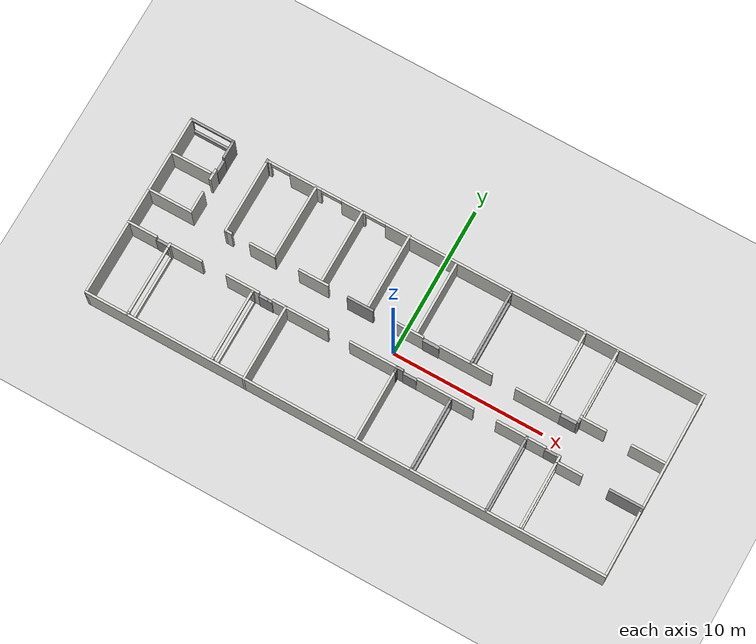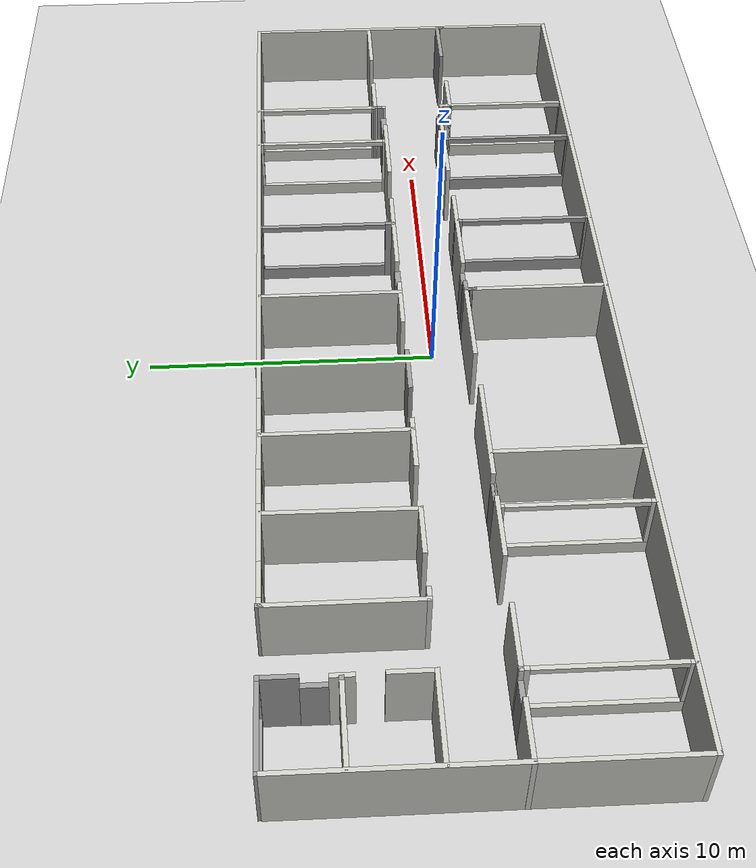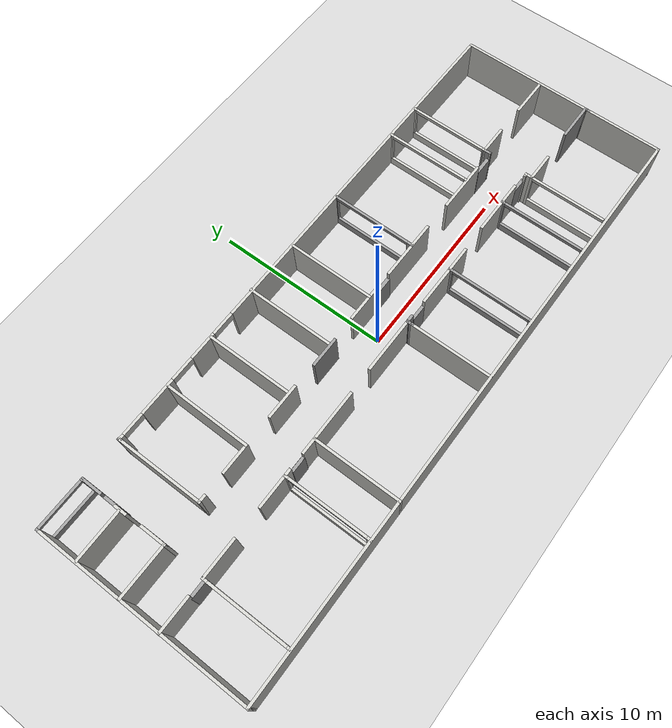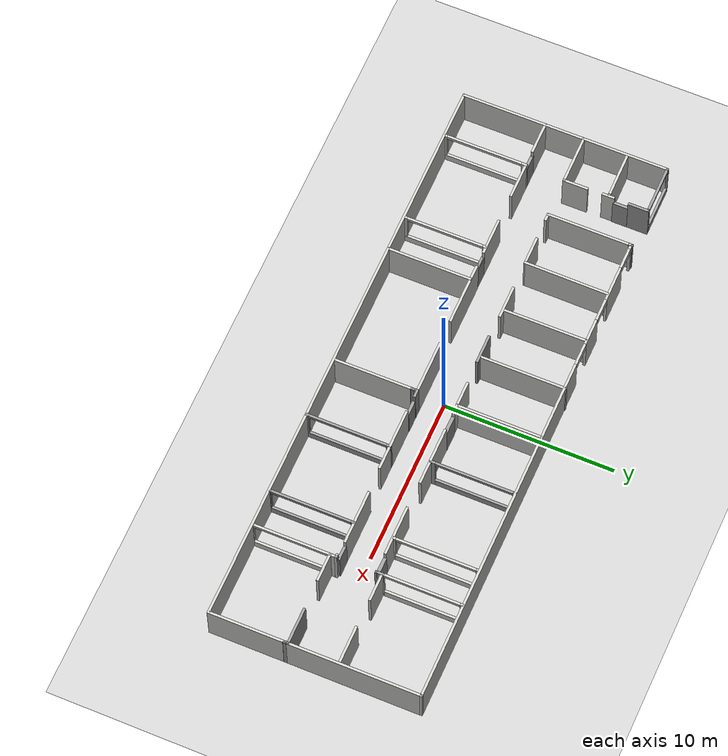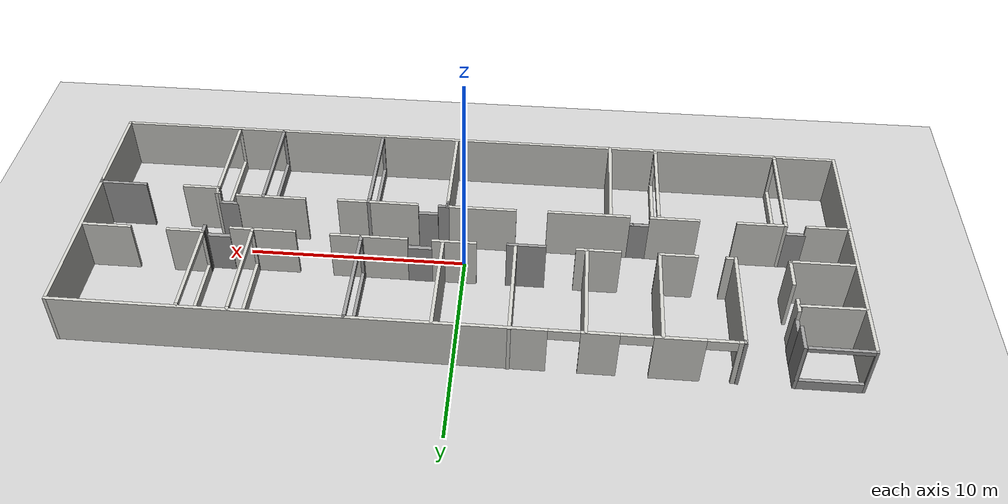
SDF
<sdf version='1.7'>
  <world name='Loyola'>
    <plugin filename="ignition-gazebo-physics-system" name="ignition::gazebo::systems::Physics" />
    <plugin filename="ignition-gazebo-user-commands-system" name="ignition::gazebo::systems::UserCommands" />
    <plugin filename="ignition-gazebo-scene-broadcaster-system" name="ignition::gazebo::systems::SceneBroadcaster" />
    <plugin filename="ignition-gazebo-sensors-system" name="ignition::gazebo::systems::Sensors"> <render_engine>ogre2</render_engine> </plugin>

    <light name='sun' type='directional'>
      <cast_shadows>1</cast_shadows>
      <pose>0 0 10 0 -0 0</pose>
      <diffuse>0.8 0.8 0.8 1</diffuse>
      <specular>0.2 0.2 0.2 1</specular>
      <attenuation>
        <range>1000</range>
        <constant>0.9</constant>
        <linear>0.01</linear>
        <quadratic>0.001</quadratic>
      </attenuation>
      <direction>-0.5 0.1 -0.9</direction>
      <spot>
        <inner_angle>0</inner_angle>
        <outer_angle>0</outer_angle>
        <falloff>0</falloff>
      </spot>
    </light>
    <model name='ground_plane'>
      <static>1</static>
      <link name='link'>
        <collision name='collision'>
          <geometry>
            <plane>
              <normal>0 0 1</normal>
              <size>100 100</size>
            </plane>
          </geometry>
          <surface>
            <contact>
              <collide_bitmask>65535</collide_bitmask>
              <ode/>
            </contact>
            <friction>
              <ode>
                <mu>100</mu>
                <mu2>50</mu2>
              </ode>
              <torsional>
                <ode/>
              </torsional>
            </friction>
            <bounce/>
          </surface>
          <max_contacts>10</max_contacts>
        </collision>
        <visual name='visual'>
          <cast_shadows>0</cast_shadows>
          <geometry>
            <plane>
              <normal>0 0 1</normal>
              <size>100 100</size>
            </plane>
          </geometry>
          <material>
            <script>
              <uri>file://media/materials/scripts/gazebo.material</uri>
              <name>Gazebo/Grey</name>
            </script>
          </material>
        </visual>
        <self_collide>0</self_collide>
        <enable_wind>0</enable_wind>
        <kinematic>0</kinematic>
      </link>
    </model>
    <gravity>0 0 -9.8</gravity>
    <magnetic_field>6e-06 2.3e-05 -4.2e-05</magnetic_field>
    <atmosphere type='adiabatic'/>
    <physics type='ode'>
      <max_step_size>0.001</max_step_size>
      <real_time_factor>1</real_time_factor>
      <real_time_update_rate>1000</real_time_update_rate>
    </physics>
    <scene>
      <ambient>0.4 0.4 0.4 1</ambient>
      <background>0.7 0.7 0.7 1</background>
      <shadows>1</shadows>
    </scene>
    <wind/>
    <spherical_coordinates>
      <surface_model>EARTH_WGS84</surface_model>
      <latitude_deg>0</latitude_deg>
      <longitude_deg>0</longitude_deg>
      <elevation>0</elevation>
      <heading_deg>0</heading_deg>
    </spherical_coordinates>
    <model name='Loyola'>
      <pose>0.011576 0.011516 0 0 -0 0</pose>
      <link name='Door_0'>
        <collision name='Door_0_Collision'>
          <geometry>
            <box>
              <size>0.9 0.17 2</size>
            </box>
          </geometry>
          <pose>0 0 1 0 -0 0</pose>
          <max_contacts>10</max_contacts>
          <surface>
            <contact>
              <ode/>
            </contact>
            <bounce/>
            <friction>
              <torsional>
                <ode/>
              </torsional>
              <ode/>
            </friction>
          </surface>
        </collision>
        <visual name='Door_0_Visual'>
          <pose>0 0 1 0 -0 0</pose>
          <geometry>
            <box>
              <size>0.9 0.17 2</size>
            </box>
          </geometry>
          <material>
            <script>
              <uri>file://media/materials/scripts/gazebo.material</uri>
              <name>Gazebo/Grey</name>
            </script>
          </material>
        </visual>
        <pose>-7.88567 -1.23425 0 0 -0 0</pose>
        <self_collide>0</self_collide>
        <enable_wind>0</enable_wind>
        <kinematic>0</kinematic>
      </link>
      <link name='Door_11'>
        <collision name='Door_11_Collision'>
          <geometry>
            <box>
              <size>0.9 0.17 2</size>
            </box>
          </geometry>
          <pose>0 0 1 0 -0 0</pose>
          <max_contacts>10</max_contacts>
          <surface>
            <contact>
              <ode/>
            </contact>
            <bounce/>
            <friction>
              <torsional>
                <ode/>
              </torsional>
              <ode/>
            </friction>
          </surface>
        </collision>
        <visual name='Door_11_Visual'>
          <pose>0 0 1 0 -0 0</pose>
          <geometry>
            <box>
              <size>0.9 0.17 2</size>
            </box>
          </geometry>
          <material>
            <script>
              <uri>file://media/materials/scripts/gazebo.material</uri>
              <name>Gazebo/Grey</name>
            </script>
          </material>
        </visual>
        <pose>1.76233 -1.19882 0 0 -0 0</pose>
        <self_collide>0</self_collide>
        <enable_wind>0</enable_wind>
        <kinematic>0</kinematic>
      </link>
      <link name='Door_12'>
        <collision name='Door_12_Collision'>
          <geometry>
            <box>
              <size>0.9 0.17 2</size>
            </box>
          </geometry>
          <pose>0 0 1 0 -0 0</pose>
          <max_contacts>10</max_contacts>
          <surface>
            <contact>
              <ode/>
            </contact>
            <bounce/>
            <friction>
              <torsional>
                <ode/>
              </torsional>
              <ode/>
            </friction>
          </surface>
        </collision>
        <visual name='Door_12_Visual'>
          <pose>0 0 1 0 -0 0</pose>
          <geometry>
            <box>
              <size>0.9 0.17 2</size>
            </box>
          </geometry>
          <material>
            <script>
              <uri>file://media/materials/scripts/gazebo.material</uri>
              <name>Gazebo/Grey</name>
            </script>
          </material>
        </visual>
        <pose>11.0856 -1.15143 0 0 -0 0</pose>
        <self_collide>0</self_collide>
        <enable_wind>0</enable_wind>
        <kinematic>0</kinematic>
      </link>
      <link name='Door_13'>
        <collision name='Door_13_Collision'>
          <geometry>
            <box>
              <size>1.06522 0.2 2</size>
            </box>
          </geometry>
          <pose>0 0 1 0 -0 0</pose>
          <max_contacts>10</max_contacts>
          <surface>
            <contact>
              <ode/>
            </contact>
            <bounce/>
            <friction>
              <torsional>
                <ode/>
              </torsional>
              <ode/>
            </friction>
          </surface>
        </collision>
        <visual name='Door_13_Visual'>
          <pose>0 0 1 0 -0 0</pose>
          <geometry>
            <box>
              <size>1.06522 0.2 2</size>
            </box>
          </geometry>
          <material>
            <script>
              <uri>file://media/materials/scripts/gazebo.material</uri>
              <name>Gazebo/Grey</name>
            </script>
          </material>
        </visual>
        <pose>11.0002 1.08329 0 0 -0 0</pose>
        <self_collide>0</self_collide>
        <enable_wind>0</enable_wind>
        <kinematic>0</kinematic>
      </link>
      <link name='Door_14'>
        <collision name='Door_14_Collision'>
          <geometry>
            <box>
              <size>1.09762 0.2 2</size>
            </box>
          </geometry>
          <pose>0 0 1 0 -0 0</pose>
          <max_contacts>10</max_contacts>
          <surface>
            <contact>
              <ode/>
            </contact>
            <bounce/>
            <friction>
              <torsional>
                <ode/>
              </torsional>
              <ode/>
            </friction>
          </surface>
        </collision>
        <visual name='Door_14_Visual'>
          <pose>0 0 1 0 -0 0</pose>
          <geometry>
            <box>
              <size>1.09762 0.2 2</size>
            </box>
          </geometry>
          <material>
            <script>
              <uri>file://media/materials/scripts/gazebo.material</uri>
              <name>Gazebo/Grey</name>
            </script>
          </material>
        </visual>
        <pose>1.89125 1.11694 0 0 -0 0</pose>
        <self_collide>0</self_collide>
        <enable_wind>0</enable_wind>
        <kinematic>0</kinematic>
      </link>
      <link name='Door_4'>
        <collision name='Door_4_Collision'>
          <geometry>
            <box>
              <size>0.9 0.17 2</size>
            </box>
          </geometry>
          <pose>0 0 1 0 -0 0</pose>
          <max_contacts>10</max_contacts>
          <surface>
            <contact>
              <ode/>
            </contact>
            <bounce/>
            <friction>
              <torsional>
                <ode/>
              </torsional>
              <ode/>
            </friction>
          </surface>
        </collision>
        <visual name='Door_4_Visual'>
          <pose>0 0 1 0 -0 0</pose>
          <geometry>
            <box>
              <size>0.9 0.17 2</size>
            </box>
          </geometry>
          <material>
            <script>
              <uri>file://media/materials/scripts/gazebo.material</uri>
              <name>Gazebo/Grey</name>
            </script>
          </material>
        </visual>
        <pose>-14.3181 4.49137 0 0 -0 1.56919</pose>
        <self_collide>0</self_collide>
        <enable_wind>0</enable_wind>
        <kinematic>0</kinematic>
      </link>
      <link name='Door_7'>
        <collision name='Door_7_Collision'>
          <geometry>
            <box>
              <size>0.9 0.17 2</size>
            </box>
          </geometry>
          <pose>0 0 1 0 -0 0</pose>
          <max_contacts>10</max_contacts>
          <surface>
            <contact>
              <ode/>
            </contact>
            <bounce/>
            <friction>
              <torsional>
                <ode/>
              </torsional>
              <ode/>
            </friction>
          </surface>
        </collision>
        <visual name='Door_7_Visual'>
          <pose>0 0 1 0 -0 0</pose>
          <geometry>
            <box>
              <size>0.9 0.17 2</size>
            </box>
          </geometry>
          <material>
            <script>
              <uri>file://media/materials/scripts/gazebo.material</uri>
              <name>Gazebo/Grey</name>
            </script>
          </material>
        </visual>
        <pose>-14.895 -1.20399 0 0 -0 0</pose>
        <self_collide>0</self_collide>
        <enable_wind>0</enable_wind>
        <kinematic>0</kinematic>
      </link>
      <link name='Door_8'>
        <collision name='Door_8_Collision'>
          <geometry>
            <box>
              <size>0.9 0.17 2</size>
            </box>
          </geometry>
          <pose>0 0 1 0 -0 0</pose>
          <max_contacts>10</max_contacts>
          <surface>
            <contact>
              <ode/>
            </contact>
            <bounce/>
            <friction>
              <torsional>
                <ode/>
              </torsional>
              <ode/>
            </friction>
          </surface>
        </collision>
        <visual name='Door_8_Visual'>
          <pose>0 0 1 0 -0 0</pose>
          <geometry>
            <box>
              <size>0.9 0.17 2</size>
            </box>
          </geometry>
          <material>
            <script>
              <uri>file://media/materials/scripts/gazebo.material</uri>
              <name>Gazebo/Grey</name>
            </script>
          </material>
        </visual>
        <pose>-7.88095 -1.22731 0 0 -0 0</pose>
        <self_collide>0</self_collide>
        <enable_wind>0</enable_wind>
        <kinematic>0</kinematic>
      </link>
      <link name='Wall_101'>
        <collision name='Wall_101_Collision'>
          <geometry>
            <box>
              <size>0.5 0.15 2.5</size>
            </box>
          </geometry>
          <pose>0 0 1.25 0 -0 0</pose>
          <max_contacts>10</max_contacts>
          <surface>
            <contact>
              <ode/>
            </contact>
            <bounce/>
            <friction>
              <torsional>
                <ode/>
              </torsional>
              <ode/>
            </friction>
          </surface>
        </collision>
        <visual name='Wall_101_Visual'>
          <pose>0 0 1.25 0 -0 0</pose>
          <geometry>
            <box>
              <size>0.5 0.15 2.5</size>
            </box>
          </geometry>
          <material>
            <script>
              <uri>file://media/materials/scripts/gazebo.material</uri>
              <name>Gazebo/CeilingTiled</name>
            </script>
            <ambient>1 1 1 1</ambient>
          </material>
          <meta>
            <layer>0</layer>
          </meta>
        </visual>
        <pose>-11.7788 1.1323 0 0 -0 3.14159</pose>
        <self_collide>0</self_collide>
        <enable_wind>0</enable_wind>
        <kinematic>0</kinematic>
      </link>
      <link name='Wall_104'>
        <collision name='Wall_104_Collision'>
          <geometry>
            <box>
              <size>5 0.15 2.5</size>
            </box>
          </geometry>
          <pose>0 0 1.25 0 -0 0</pose>
          <max_contacts>10</max_contacts>
          <surface>
            <contact>
              <ode/>
            </contact>
            <bounce/>
            <friction>
              <torsional>
                <ode/>
              </torsional>
              <ode/>
            </friction>
          </surface>
        </collision>
        <visual name='Wall_104_Visual'>
          <pose>0 0 1.25 0 -0 0</pose>
          <geometry>
            <box>
              <size>5 0.15 2.5</size>
            </box>
          </geometry>
          <material>
            <script>
              <uri>file://media/materials/scripts/gazebo.material</uri>
              <name>Gazebo/CeilingTiled</name>
            </script>
            <ambient>1 1 1 1</ambient>
          </material>
          <meta>
            <layer>0</layer>
          </meta>
        </visual>
        <pose>-11.9538 3.5573 0 0 -0 1.5708</pose>
        <self_collide>0</self_collide>
        <enable_wind>0</enable_wind>
        <kinematic>0</kinematic>
      </link>
      <link name='Wall_105'>
        <collision name='Wall_105_Collision'>
          <geometry>
            <box>
              <size>0.25 0.15 2.5</size>
            </box>
          </geometry>
          <pose>0 0 1.25 0 -0 0</pose>
          <max_contacts>10</max_contacts>
          <surface>
            <contact>
              <ode/>
            </contact>
            <bounce/>
            <friction>
              <torsional>
                <ode/>
              </torsional>
              <ode/>
            </friction>
          </surface>
        </collision>
        <visual name='Wall_105_Visual'>
          <pose>0 0 1.25 0 -0 0</pose>
          <geometry>
            <box>
              <size>0.25 0.15 2.5</size>
            </box>
          </geometry>
          <material>
            <script>
              <uri>file://media/materials/scripts/gazebo.material</uri>
              <name>Gazebo/Grey</name>
            </script>
            <ambient>1 1 1 1</ambient>
          </material>
          <meta>
            <layer>0</layer>
          </meta>
        </visual>
        <pose>-11.9538 6.03231 0 0 -0 1.5708</pose>
        <self_collide>0</self_collide>
        <enable_wind>0</enable_wind>
        <kinematic>0</kinematic>
      </link>
      <link name='Wall_110'>
        <collision name='Wall_110_Collision'>
          <geometry>
            <box>
              <size>0.15 0.15 2.5</size>
            </box>
          </geometry>
          <pose>0 0 1.25 0 -0 0</pose>
          <max_contacts>10</max_contacts>
          <surface>
            <contact>
              <ode/>
            </contact>
            <bounce/>
            <friction>
              <torsional>
                <ode/>
              </torsional>
              <ode/>
            </friction>
          </surface>
        </collision>
        <visual name='Wall_110_Visual'>
          <pose>0 0 1.25 0 -0 0</pose>
          <geometry>
            <box>
              <size>0.15 0.15 2.5</size>
            </box>
          </geometry>
          <material>
            <script>
              <uri>file://media/materials/scripts/gazebo.material</uri>
              <name>Gazebo/Grey</name>
            </script>
            <ambient>1 1 1 1</ambient>
          </material>
          <meta>
            <layer>0</layer>
          </meta>
        </visual>
        <pose>-14.4103 3.76218 0 0 -0 0</pose>
        <self_collide>0</self_collide>
        <enable_wind>0</enable_wind>
        <kinematic>0</kinematic>
      </link>
      <link name='Wall_113'>
        <collision name='Wall_113_Collision'>
          <geometry>
            <box>
              <size>0.75 0.15 2.5</size>
            </box>
          </geometry>
          <pose>0 0 1.25 0 -0 0</pose>
          <max_contacts>10</max_contacts>
          <surface>
            <contact>
              <ode/>
            </contact>
            <bounce/>
            <friction>
              <torsional>
                <ode/>
              </torsional>
              <ode/>
            </friction>
          </surface>
        </collision>
        <visual name='Wall_113_Visual'>
          <pose>0 0 1.25 0 -0 0</pose>
          <geometry>
            <box>
              <size>0.75 0.15 2.5</size>
            </box>
          </geometry>
          <material>
            <script>
              <uri>file://media/materials/scripts/gazebo.material</uri>
              <name>Gazebo/CeilingTiled</name>
            </script>
            <ambient>1 1 1 1</ambient>
          </material>
          <meta>
            <layer>0</layer>
          </meta>
        </visual>
        <pose>-14.3366 3.74353 0 0 -0 -1.5708</pose>
        <self_collide>0</self_collide>
        <enable_wind>0</enable_wind>
        <kinematic>0</kinematic>
      </link>
      <link name='Wall_115'>
        <collision name='Wall_115_Collision'>
          <geometry>
            <box>
              <size>2.85056 0.15 2.5</size>
            </box>
          </geometry>
          <pose>0 0 1.25 0 -0 0</pose>
          <max_contacts>10</max_contacts>
          <surface>
            <contact>
              <ode/>
            </contact>
            <bounce/>
            <friction>
              <torsional>
                <ode/>
              </torsional>
              <ode/>
            </friction>
          </surface>
        </collision>
        <visual name='Wall_115_Visual'>
          <pose>0 0 1.25 0 -0 0</pose>
          <geometry>
            <box>
              <size>2.85056 0.15 2.5</size>
            </box>
          </geometry>
          <material>
            <script>
              <uri>file://media/materials/scripts/gazebo.material</uri>
              <name>Gazebo/CeilingTiled</name>
            </script>
            <ambient>1 1 1 1</ambient>
          </material>
          <meta>
            <layer>0</layer>
          </meta>
        </visual>
        <pose>-15.7606 3.75157 0 0 -0 0.007857</pose>
        <self_collide>0</self_collide>
        <enable_wind>0</enable_wind>
        <kinematic>0</kinematic>
      </link>
      <link name='Wall_118'>
        <collision name='Wall_118_Collision'>
          <geometry>
            <box>
              <size>12.25 0.15 2.5</size>
            </box>
          </geometry>
          <pose>0 0 1.25 0 -0 0</pose>
          <max_contacts>10</max_contacts>
          <surface>
            <contact>
              <ode/>
            </contact>
            <bounce/>
            <friction>
              <torsional>
                <ode/>
              </torsional>
              <ode/>
            </friction>
          </surface>
        </collision>
        <visual name='Wall_118_Visual'>
          <pose>0 0 1.25 0 -0 0</pose>
          <geometry>
            <box>
              <size>12.25 0.15 2.5</size>
            </box>
          </geometry>
          <material>
            <script>
              <uri>file://media/materials/scripts/gazebo.material</uri>
              <name>Gazebo/CeilingTiled</name>
            </script>
            <ambient>1 1 1 1</ambient>
          </material>
          <meta>
            <layer>0</layer>
          </meta>
        </visual>
        <pose>-17.1766 -0.048952 0 0 -0 1.5708</pose>
        <self_collide>0</self_collide>
        <enable_wind>0</enable_wind>
        <kinematic>0</kinematic>
      </link>
      <link name='Wall_12'>
        <collision name='Wall_12_Collision'>
          <geometry>
            <box>
              <size>7.75 0.15 2.5</size>
            </box>
          </geometry>
          <pose>0 0 1.25 0 -0 0</pose>
          <max_contacts>10</max_contacts>
          <surface>
            <contact>
              <ode/>
            </contact>
            <bounce/>
            <friction>
              <torsional>
                <ode/>
              </torsional>
              <ode/>
            </friction>
          </surface>
        </collision>
        <visual name='Wall_12_Visual'>
          <pose>0 0 1.25 0 -0 0</pose>
          <geometry>
            <box>
              <size>7.75 0.15 2.5</size>
            </box>
          </geometry>
          <material>
            <script>
              <uri>file://media/materials/scripts/gazebo.material</uri>
              <name>Gazebo/CeilingTiled</name>
            </script>
            <ambient>1 1 1 1</ambient>
          </material>
          <meta>
            <layer>0</layer>
          </meta>
        </visual>
        <pose>17.1864 2.25105 0 0 -0 1.5708</pose>
        <self_collide>0</self_collide>
        <enable_wind>0</enable_wind>
        <kinematic>0</kinematic>
      </link>
      <link name='Wall_120'>
        <collision name='Wall_120_Collision'>
          <geometry>
            <box>
              <size>2 0.15 2.5</size>
            </box>
          </geometry>
          <pose>0 0 1.25 0 -0 0</pose>
          <max_contacts>10</max_contacts>
          <surface>
            <contact>
              <ode/>
            </contact>
            <bounce/>
            <friction>
              <torsional>
                <ode/>
              </torsional>
              <ode/>
            </friction>
          </surface>
        </collision>
        <visual name='Wall_120_Visual'>
          <pose>0 0 1.25 0 -0 0</pose>
          <geometry>
            <box>
              <size>2 0.15 2.5</size>
            </box>
          </geometry>
          <material>
            <script>
              <uri>file://media/materials/scripts/gazebo.material</uri>
              <name>Gazebo/CeilingTiled</name>
            </script>
            <ambient>1 1 1 1</ambient>
          </material>
          <meta>
            <layer>0</layer>
          </meta>
        </visual>
        <pose>-16.2614 -1.19554 0 0 -0 3.14159</pose>
        <self_collide>0</self_collide>
        <enable_wind>0</enable_wind>
        <kinematic>0</kinematic>
      </link>
      <link name='Wall_124'>
        <collision name='Wall_124_Collision'>
          <geometry>
            <box>
              <size>0.5 0.15 2.5</size>
            </box>
          </geometry>
          <pose>0 0 1.25 0 -0 0</pose>
          <max_contacts>10</max_contacts>
          <surface>
            <contact>
              <ode/>
            </contact>
            <bounce/>
            <friction>
              <torsional>
                <ode/>
              </torsional>
              <ode/>
            </friction>
          </surface>
        </collision>
        <visual name='Wall_124_Visual'>
          <pose>0 0 1.25 0 -0 0</pose>
          <geometry>
            <box>
              <size>0.5 0.15 2.5</size>
            </box>
          </geometry>
          <material>
            <script>
              <uri>file://media/materials/scripts/gazebo.material</uri>
              <name>Gazebo/Grey</name>
            </script>
            <ambient>1 1 1 1</ambient>
          </material>
          <meta>
            <layer>0</layer>
          </meta>
        </visual>
        <pose>1.05325 -1.18357 0 0 -0 0</pose>
        <self_collide>0</self_collide>
        <enable_wind>0</enable_wind>
        <kinematic>0</kinematic>
      </link>
      <link name='Wall_126'>
        <collision name='Wall_126_Collision'>
          <geometry>
            <box>
              <size>0.15 0.15 2.5</size>
            </box>
          </geometry>
          <pose>0 0 1.25 0 -0 0</pose>
          <max_contacts>10</max_contacts>
          <surface>
            <contact>
              <ode/>
            </contact>
            <bounce/>
            <friction>
              <torsional>
                <ode/>
              </torsional>
              <ode/>
            </friction>
          </surface>
        </collision>
        <visual name='Wall_126_Visual'>
          <pose>0 0 1.25 0 -0 0</pose>
          <geometry>
            <box>
              <size>0.15 0.15 2.5</size>
            </box>
          </geometry>
          <material>
            <script>
              <uri>file://media/materials/scripts/gazebo.material</uri>
              <name>Gazebo/CeilingTiled</name>
            </script>
            <ambient>1 1 1 1</ambient>
          </material>
          <meta>
            <layer>0</layer>
          </meta>
        </visual>
        <pose>11.5977 1.07049 0 0 -0 0</pose>
        <self_collide>0</self_collide>
        <enable_wind>0</enable_wind>
        <kinematic>0</kinematic>
      </link>
      <link name='Wall_13'>
        <pose>2.63637 6.05105 0 0 -0 3.14159</pose>
        <visual name='Wall_13_Visual_0'>
          <pose>-4.02332 0 1.25 0 -0 0</pose>
          <geometry>
            <box>
              <size>21.2034 0.15 2.5</size>
            </box>
          </geometry>
          <material>
            <script>
              <uri>file://media/materials/scripts/gazebo.material</uri>
              <name>Gazebo/CeilingTiled</name>
            </script>
            <ambient>1 1 1 1</ambient>
          </material>
          <meta>
            <layer>0</layer>
          </meta>
        </visual>
        <collision name='Wall_13_Collision_0'>
          <geometry>
            <box>
              <size>21.2034 0.15 2.5</size>
            </box>
          </geometry>
          <pose>-4.02332 0 1.25 0 -0 0</pose>
          <max_contacts>10</max_contacts>
          <surface>
            <contact>
              <ode/>
            </contact>
            <bounce/>
            <friction>
              <torsional>
                <ode/>
              </torsional>
              <ode/>
            </friction>
          </surface>
        </collision>
        <visual name='Wall_13_Visual_1'>
          <pose>8.7334 0 1.25 0 -0 0</pose>
          <geometry>
            <box>
              <size>1.61371 0.15 2.5</size>
            </box>
          </geometry>
          <material>
            <script>
              <uri>file://media/materials/scripts/gazebo.material</uri>
              <name>Gazebo/CeilingTiled</name>
            </script>
            <ambient>1 1 1 1</ambient>
          </material>
          <meta>
            <layer>0</layer>
          </meta>
        </visual>
        <collision name='Wall_13_Collision_1'>
          <geometry>
            <box>
              <size>1.61371 0.15 2.5</size>
            </box>
          </geometry>
          <pose>8.7334 0 1.25 0 -0 0</pose>
          <max_contacts>10</max_contacts>
          <surface>
            <contact>
              <ode/>
            </contact>
            <bounce/>
            <friction>
              <torsional>
                <ode/>
              </torsional>
              <ode/>
            </friction>
          </surface>
        </collision>
        <visual name='Wall_13_Visual_2'>
          <pose>11.9771 0 1.25 0 -0 0</pose>
          <geometry>
            <box>
              <size>2.13835 0.15 2.5</size>
            </box>
          </geometry>
          <material>
            <script>
              <uri>file://media/materials/scripts/gazebo.material</uri>
              <name>Gazebo/CeilingTiled</name>
            </script>
            <ambient>1 1 1 1</ambient>
          </material>
          <meta>
            <layer>0</layer>
          </meta>
        </visual>
        <collision name='Wall_13_Collision_2'>
          <geometry>
            <box>
              <size>2.13835 0.15 2.5</size>
            </box>
          </geometry>
          <pose>11.9771 0 1.25 0 -0 0</pose>
          <max_contacts>10</max_contacts>
          <surface>
            <contact>
              <ode/>
            </contact>
            <bounce/>
            <friction>
              <torsional>
                <ode/>
              </torsional>
              <ode/>
            </friction>
          </surface>
        </collision>
        <visual name='Wall_13_Visual_3'>
          <pose>14.4717 0 1.25 0 -0 0</pose>
          <geometry>
            <box>
              <size>0.30661 0.15 2.5</size>
            </box>
          </geometry>
          <material>
            <script>
              <uri>file://media/materials/scripts/gazebo.material</uri>
              <name>Gazebo/CeilingTiled</name>
            </script>
            <ambient>1 1 1 1</ambient>
          </material>
          <meta>
            <layer>0</layer>
          </meta>
        </visual>
        <collision name='Wall_13_Collision_3'>
          <geometry>
            <box>
              <size>0.30661 0.15 2.5</size>
            </box>
          </geometry>
          <pose>14.4717 0 1.25 0 -0 0</pose>
          <max_contacts>10</max_contacts>
          <surface>
            <contact>
              <ode/>
            </contact>
            <bounce/>
            <friction>
              <torsional>
                <ode/>
              </torsional>
              <ode/>
            </friction>
          </surface>
        </collision>
        <visual name='Wall_13_Visual_4'>
          <pose>7.25245 0 2.25 0 -0 0</pose>
          <geometry>
            <box>
              <size>1.34818 0.15 0.5</size>
            </box>
          </geometry>
          <material>
            <script>
              <uri>file://media/materials/scripts/gazebo.material</uri>
              <name>Gazebo/CeilingTiled</name>
            </script>
            <ambient>1 1 1 1</ambient>
          </material>
          <meta>
            <layer>0</layer>
          </meta>
        </visual>
        <collision name='Wall_13_Collision_4'>
          <geometry>
            <box>
              <size>1.34818 0.15 0.5</size>
            </box>
          </geometry>
          <pose>7.25245 0 2.25 0 -0 0</pose>
          <max_contacts>10</max_contacts>
          <surface>
            <contact>
              <ode/>
            </contact>
            <bounce/>
            <friction>
              <torsional>
                <ode/>
              </torsional>
              <ode/>
            </friction>
          </surface>
        </collision>
        <visual name='Wall_13_Visual_5'>
          <pose>10.2241 0 2.25 0 -0 0</pose>
          <geometry>
            <box>
              <size>1.36767 0.15 0.5</size>
            </box>
          </geometry>
          <material>
            <script>
              <uri>file://media/materials/scripts/gazebo.material</uri>
              <name>Gazebo/CeilingTiled</name>
            </script>
            <ambient>1 1 1 1</ambient>
          </material>
          <meta>
            <layer>0</layer>
          </meta>
        </visual>
        <collision name='Wall_13_Collision_5'>
          <geometry>
            <box>
              <size>1.36767 0.15 0.5</size>
            </box>
          </geometry>
          <pose>10.2241 0 2.25 0 -0 0</pose>
          <max_contacts>10</max_contacts>
          <surface>
            <contact>
              <ode/>
            </contact>
            <bounce/>
            <friction>
              <torsional>
                <ode/>
              </torsional>
              <ode/>
            </friction>
          </surface>
        </collision>
        <visual name='Wall_13_Visual_6'>
          <pose>13.6823 0 2.25 0 -0 0</pose>
          <geometry>
            <box>
              <size>1.27212 0.15 0.5</size>
            </box>
          </geometry>
          <material>
            <script>
              <uri>file://media/materials/scripts/gazebo.material</uri>
              <name>Gazebo/CeilingTiled</name>
            </script>
            <ambient>1 1 1 1</ambient>
          </material>
          <meta>
            <layer>0</layer>
          </meta>
        </visual>
        <collision name='Wall_13_Collision_6'>
          <geometry>
            <box>
              <size>1.27212 0.15 0.5</size>
            </box>
          </geometry>
          <pose>13.6823 0 2.25 0 -0 0</pose>
          <max_contacts>10</max_contacts>
          <surface>
            <contact>
              <ode/>
            </contact>
            <bounce/>
            <friction>
              <torsional>
                <ode/>
              </torsional>
              <ode/>
            </friction>
          </surface>
        </collision>
        <self_collide>0</self_collide>
        <enable_wind>0</enable_wind>
        <kinematic>0</kinematic>
      </link>
      <link name='Wall_132'>
        <collision name='Wall_132_Collision'>
          <geometry>
            <box>
              <size>1.75 0.15 2.5</size>
            </box>
          </geometry>
          <pose>0 0 1.25 0 -0 0</pose>
          <max_contacts>10</max_contacts>
          <surface>
            <contact>
              <ode/>
            </contact>
            <bounce/>
            <friction>
              <torsional>
                <ode/>
              </torsional>
              <ode/>
            </friction>
          </surface>
        </collision>
        <visual name='Wall_132_Visual'>
          <pose>0 0 1.25 0 -0 0</pose>
          <geometry>
            <box>
              <size>1.75 0.15 2.5</size>
            </box>
          </geometry>
          <material>
            <script>
              <uri>file://media/materials/scripts/gazebo.material</uri>
              <name>Gazebo/CeilingTiled</name>
            </script>
            <ambient>1 1 1 1</ambient>
          </material>
          <meta>
            <layer>0</layer>
          </meta>
        </visual>
        <pose>12.3958 1.40203 0 0 -0 3.14159</pose>
        <self_collide>0</self_collide>
        <enable_wind>0</enable_wind>
        <kinematic>0</kinematic>
      </link>
      <link name='Wall_134'>
        <collision name='Wall_134_Collision'>
          <geometry>
            <box>
              <size>0.15 0.15 2.5</size>
            </box>
          </geometry>
          <pose>0 0 1.25 0 -0 0</pose>
          <max_contacts>10</max_contacts>
          <surface>
            <contact>
              <ode/>
            </contact>
            <bounce/>
            <friction>
              <torsional>
                <ode/>
              </torsional>
              <ode/>
            </friction>
          </surface>
        </collision>
        <visual name='Wall_134_Visual'>
          <pose>0 0 1.25 0 -0 0</pose>
          <geometry>
            <box>
              <size>0.15 0.15 2.5</size>
            </box>
          </geometry>
          <material>
            <script>
              <uri>file://media/materials/scripts/gazebo.material</uri>
              <name>Gazebo/Grey</name>
            </script>
            <ambient>1 1 1 1</ambient>
          </material>
          <meta>
            <layer>0</layer>
          </meta>
        </visual>
        <pose>11.5977 1.07049 0 0 -0 0</pose>
        <self_collide>0</self_collide>
        <enable_wind>0</enable_wind>
        <kinematic>0</kinematic>
      </link>
      <link name='Wall_136'>
        <collision name='Wall_136_Collision'>
          <geometry>
            <box>
              <size>0.48154 0.15 2.5</size>
            </box>
          </geometry>
          <pose>0 0 1.25 0 -0 0</pose>
          <max_contacts>10</max_contacts>
          <surface>
            <contact>
              <ode/>
            </contact>
            <bounce/>
            <friction>
              <torsional>
                <ode/>
              </torsional>
              <ode/>
            </friction>
          </surface>
        </collision>
        <visual name='Wall_136_Visual'>
          <pose>0 0 1.25 0 -0 0</pose>
          <geometry>
            <box>
              <size>0.48154 0.15 2.5</size>
            </box>
          </geometry>
          <material>
            <script>
              <uri>file://media/materials/scripts/gazebo.material</uri>
              <name>Gazebo/Grey</name>
            </script>
            <ambient>1 1 1 1</ambient>
          </material>
          <meta>
            <layer>0</layer>
          </meta>
        </visual>
        <pose>11.5968 1.23626 0 0 -0 -1.56493</pose>
        <self_collide>0</self_collide>
        <enable_wind>0</enable_wind>
        <kinematic>0</kinematic>
      </link>
      <link name='Wall_138'>
        <pose>-14.3764 -3.61957 0 0 -0 -1.5708</pose>
        <visual name='Wall_138_Visual_0'>
          <pose>-2.34104 0 1.25 0 -0 0</pose>
          <geometry>
            <box>
              <size>0.317931 0.15 2.5</size>
            </box>
          </geometry>
          <material>
            <script>
              <uri>file://media/materials/scripts/gazebo.material</uri>
              <name>Gazebo/CeilingTiled</name>
            </script>
            <ambient>1 1 1 1</ambient>
          </material>
          <meta>
            <layer>0</layer>
          </meta>
        </visual>
        <collision name='Wall_138_Collision_0'>
          <geometry>
            <box>
              <size>0.317931 0.15 2.5</size>
            </box>
          </geometry>
          <pose>-2.34104 0 1.25 0 -0 0</pose>
          <max_contacts>10</max_contacts>
          <surface>
            <contact>
              <ode/>
            </contact>
            <bounce/>
            <friction>
              <torsional>
                <ode/>
              </torsional>
              <ode/>
            </friction>
          </surface>
        </collision>
        <visual name='Wall_138_Visual_1'>
          <pose>0.158965 0 0.25 0 -0 0</pose>
          <geometry>
            <box>
              <size>4.68207 0.15 0.5</size>
            </box>
          </geometry>
          <material>
            <script>
              <uri>file://media/materials/scripts/gazebo.material</uri>
              <name>Gazebo/CeilingTiled</name>
            </script>
            <ambient>1 1 1 1</ambient>
          </material>
          <meta>
            <layer>0</layer>
          </meta>
        </visual>
        <collision name='Wall_138_Collision_1'>
          <geometry>
            <box>
              <size>4.68207 0.15 0.5</size>
            </box>
          </geometry>
          <pose>0.158965 0 0.25 0 -0 0</pose>
          <max_contacts>10</max_contacts>
          <surface>
            <contact>
              <ode/>
            </contact>
            <bounce/>
            <friction>
              <torsional>
                <ode/>
              </torsional>
              <ode/>
            </friction>
          </surface>
        </collision>
        <visual name='Wall_138_Visual_2'>
          <pose>2.39397 0 1.5 0 -0 0</pose>
          <geometry>
            <box>
              <size>0.212069 0.15 2</size>
            </box>
          </geometry>
          <material>
            <script>
              <uri>file://media/materials/scripts/gazebo.material</uri>
              <name>Gazebo/CeilingTiled</name>
            </script>
            <ambient>1 1 1 1</ambient>
          </material>
          <meta>
            <layer>0</layer>
          </meta>
        </visual>
        <collision name='Wall_138_Collision_2'>
          <geometry>
            <box>
              <size>0.212069 0.15 2</size>
            </box>
          </geometry>
          <pose>2.39397 0 1.5 0 -0 0</pose>
          <max_contacts>10</max_contacts>
          <surface>
            <contact>
              <ode/>
            </contact>
            <bounce/>
            <friction>
              <torsional>
                <ode/>
              </torsional>
              <ode/>
            </friction>
          </surface>
        </collision>
        <visual name='Wall_138_Visual_3'>
          <pose>0.052931 0 2.4 0 -0 0</pose>
          <geometry>
            <box>
              <size>4.47 0.15 0.2</size>
            </box>
          </geometry>
          <material>
            <script>
              <uri>file://media/materials/scripts/gazebo.material</uri>
              <name>Gazebo/CeilingTiled</name>
            </script>
            <ambient>1 1 1 1</ambient>
          </material>
          <meta>
            <layer>0</layer>
          </meta>
        </visual>
        <collision name='Wall_138_Collision_3'>
          <geometry>
            <box>
              <size>4.47 0.15 0.2</size>
            </box>
          </geometry>
          <pose>0.052931 0 2.4 0 -0 0</pose>
          <max_contacts>10</max_contacts>
          <surface>
            <contact>
              <ode/>
            </contact>
            <bounce/>
            <friction>
              <torsional>
                <ode/>
              </torsional>
              <ode/>
            </friction>
          </surface>
        </collision>
        <self_collide>0</self_collide>
        <enable_wind>0</enable_wind>
        <kinematic>0</kinematic>
      </link>
      <link name='Wall_140'>
        <pose>4.5175 -3.63037 0 0 -0 -1.5708</pose>
        <visual name='Wall_140_Visual_0'>
          <pose>-2.36498 0 1.25 0 -0 0</pose>
          <geometry>
            <box>
              <size>0.270042 0.15 2.5</size>
            </box>
          </geometry>
          <material>
            <script>
              <uri>file://media/materials/scripts/gazebo.material</uri>
              <name>Gazebo/Grey</name>
            </script>
            <ambient>1 1 1 1</ambient>
          </material>
          <meta>
            <layer>0</layer>
          </meta>
        </visual>
        <collision name='Wall_140_Collision_0'>
          <geometry>
            <box>
              <size>0.270042 0.15 2.5</size>
            </box>
          </geometry>
          <pose>-2.36498 0 1.25 0 -0 0</pose>
          <max_contacts>10</max_contacts>
          <surface>
            <contact>
              <ode/>
            </contact>
            <bounce/>
            <friction>
              <torsional>
                <ode/>
              </torsional>
              <ode/>
            </friction>
          </surface>
        </collision>
        <visual name='Wall_140_Visual_1'>
          <pose>0.135021 0 0.25 0 -0 0</pose>
          <geometry>
            <box>
              <size>4.72996 0.15 0.5</size>
            </box>
          </geometry>
          <material>
            <script>
              <uri>file://media/materials/scripts/gazebo.material</uri>
              <name>Gazebo/Grey</name>
            </script>
            <ambient>1 1 1 1</ambient>
          </material>
          <meta>
            <layer>0</layer>
          </meta>
        </visual>
        <collision name='Wall_140_Collision_1'>
          <geometry>
            <box>
              <size>4.72996 0.15 0.5</size>
            </box>
          </geometry>
          <pose>0.135021 0 0.25 0 -0 0</pose>
          <max_contacts>10</max_contacts>
          <surface>
            <contact>
              <ode/>
            </contact>
            <bounce/>
            <friction>
              <torsional>
                <ode/>
              </torsional>
              <ode/>
            </friction>
          </surface>
        </collision>
        <visual name='Wall_140_Visual_2'>
          <pose>2.40552 0 1.5 0 -0 0</pose>
          <geometry>
            <box>
              <size>0.188958 0.15 2</size>
            </box>
          </geometry>
          <material>
            <script>
              <uri>file://media/materials/scripts/gazebo.material</uri>
              <name>Gazebo/Grey</name>
            </script>
            <ambient>1 1 1 1</ambient>
          </material>
          <meta>
            <layer>0</layer>
          </meta>
        </visual>
        <collision name='Wall_140_Collision_2'>
          <geometry>
            <box>
              <size>0.188958 0.15 2</size>
            </box>
          </geometry>
          <pose>2.40552 0 1.5 0 -0 0</pose>
          <max_contacts>10</max_contacts>
          <surface>
            <contact>
              <ode/>
            </contact>
            <bounce/>
            <friction>
              <torsional>
                <ode/>
              </torsional>
              <ode/>
            </friction>
          </surface>
        </collision>
        <visual name='Wall_140_Visual_3'>
          <pose>0.040542 0 2.4 0 -0 0</pose>
          <geometry>
            <box>
              <size>4.541 0.15 0.2</size>
            </box>
          </geometry>
          <material>
            <script>
              <uri>file://media/materials/scripts/gazebo.material</uri>
              <name>Gazebo/Grey</name>
            </script>
            <ambient>1 1 1 1</ambient>
          </material>
          <meta>
            <layer>0</layer>
          </meta>
        </visual>
        <collision name='Wall_140_Collision_3'>
          <geometry>
            <box>
              <size>4.541 0.15 0.2</size>
            </box>
          </geometry>
          <pose>0.040542 0 2.4 0 -0 0</pose>
          <max_contacts>10</max_contacts>
          <surface>
            <contact>
              <ode/>
            </contact>
            <bounce/>
            <friction>
              <torsional>
                <ode/>
              </torsional>
              <ode/>
            </friction>
          </surface>
        </collision>
        <self_collide>0</self_collide>
        <enable_wind>0</enable_wind>
        <kinematic>0</kinematic>
      </link>
      <link name='Wall_143'>
        <pose>9.43238 -3.62443 0 0 -0 -1.5708</pose>
        <visual name='Wall_143_Visual_0'>
          <pose>-2.39953 0 1.25 0 -0 0</pose>
          <geometry>
            <box>
              <size>0.200941 0.15 2.5</size>
            </box>
          </geometry>
          <material>
            <script>
              <uri>file://media/materials/scripts/gazebo.material</uri>
              <name>Gazebo/Grey</name>
            </script>
            <ambient>1 1 1 1</ambient>
          </material>
          <meta>
            <layer>0</layer>
          </meta>
        </visual>
        <collision name='Wall_143_Collision_0'>
          <geometry>
            <box>
              <size>0.200941 0.15 2.5</size>
            </box>
          </geometry>
          <pose>-2.39953 0 1.25 0 -0 0</pose>
          <max_contacts>10</max_contacts>
          <surface>
            <contact>
              <ode/>
            </contact>
            <bounce/>
            <friction>
              <torsional>
                <ode/>
              </torsional>
              <ode/>
            </friction>
          </surface>
        </collision>
        <visual name='Wall_143_Visual_1'>
          <pose>0.10047 0 0.25 0 -0 0</pose>
          <geometry>
            <box>
              <size>4.79906 0.15 0.5</size>
            </box>
          </geometry>
          <material>
            <script>
              <uri>file://media/materials/scripts/gazebo.material</uri>
              <name>Gazebo/Grey</name>
            </script>
            <ambient>1 1 1 1</ambient>
          </material>
          <meta>
            <layer>0</layer>
          </meta>
        </visual>
        <collision name='Wall_143_Collision_1'>
          <geometry>
            <box>
              <size>4.79906 0.15 0.5</size>
            </box>
          </geometry>
          <pose>0.10047 0 0.25 0 -0 0</pose>
          <max_contacts>10</max_contacts>
          <surface>
            <contact>
              <ode/>
            </contact>
            <bounce/>
            <friction>
              <torsional>
                <ode/>
              </torsional>
              <ode/>
            </friction>
          </surface>
        </collision>
        <visual name='Wall_143_Visual_2'>
          <pose>2.42347 0 1.5 0 -0 0</pose>
          <geometry>
            <box>
              <size>0.153059 0.15 2</size>
            </box>
          </geometry>
          <material>
            <script>
              <uri>file://media/materials/scripts/gazebo.material</uri>
              <name>Gazebo/Grey</name>
            </script>
            <ambient>1 1 1 1</ambient>
          </material>
          <meta>
            <layer>0</layer>
          </meta>
        </visual>
        <collision name='Wall_143_Collision_2'>
          <geometry>
            <box>
              <size>0.153059 0.15 2</size>
            </box>
          </geometry>
          <pose>2.42347 0 1.5 0 -0 0</pose>
          <max_contacts>10</max_contacts>
          <surface>
            <contact>
              <ode/>
            </contact>
            <bounce/>
            <friction>
              <torsional>
                <ode/>
              </torsional>
              <ode/>
            </friction>
          </surface>
        </collision>
        <visual name='Wall_143_Visual_3'>
          <pose>0.023941 0 2.4 0 -0 0</pose>
          <geometry>
            <box>
              <size>4.646 0.15 0.2</size>
            </box>
          </geometry>
          <material>
            <script>
              <uri>file://media/materials/scripts/gazebo.material</uri>
              <name>Gazebo/Grey</name>
            </script>
            <ambient>1 1 1 1</ambient>
          </material>
          <meta>
            <layer>0</layer>
          </meta>
        </visual>
        <collision name='Wall_143_Collision_3'>
          <geometry>
            <box>
              <size>4.646 0.15 0.2</size>
            </box>
          </geometry>
          <pose>0.023941 0 2.4 0 -0 0</pose>
          <max_contacts>10</max_contacts>
          <surface>
            <contact>
              <ode/>
            </contact>
            <bounce/>
            <friction>
              <torsional>
                <ode/>
              </torsional>
              <ode/>
            </friction>
          </surface>
        </collision>
        <self_collide>0</self_collide>
        <enable_wind>0</enable_wind>
        <kinematic>0</kinematic>
      </link>
      <link name='Wall_145'>
        <pose>11.6228 -3.76099 0 0 -0 -1.5708</pose>
        <visual name='Wall_145_Visual_0'>
          <pose>-2.18309 0 1.25 0 -0 0</pose>
          <geometry>
            <box>
              <size>0.133827 0.15 2.5</size>
            </box>
          </geometry>
          <material>
            <script>
              <uri>file://media/materials/scripts/gazebo.material</uri>
              <name>Gazebo/CeilingTiled</name>
            </script>
            <ambient>1 1 1 1</ambient>
          </material>
          <meta>
            <layer>0</layer>
          </meta>
        </visual>
        <collision name='Wall_145_Collision_0'>
          <geometry>
            <box>
              <size>0.133827 0.15 2.5</size>
            </box>
          </geometry>
          <pose>-2.18309 0 1.25 0 -0 0</pose>
          <max_contacts>10</max_contacts>
          <surface>
            <contact>
              <ode/>
            </contact>
            <bounce/>
            <friction>
              <torsional>
                <ode/>
              </torsional>
              <ode/>
            </friction>
          </surface>
        </collision>
        <visual name='Wall_145_Visual_1'>
          <pose>0.066914 0 0.25 0 -0 0</pose>
          <geometry>
            <box>
              <size>4.36617 0.15 0.5</size>
            </box>
          </geometry>
          <material>
            <script>
              <uri>file://media/materials/scripts/gazebo.material</uri>
              <name>Gazebo/CeilingTiled</name>
            </script>
            <ambient>1 1 1 1</ambient>
          </material>
          <meta>
            <layer>0</layer>
          </meta>
        </visual>
        <collision name='Wall_145_Collision_1'>
          <geometry>
            <box>
              <size>4.36617 0.15 0.5</size>
            </box>
          </geometry>
          <pose>0.066914 0 0.25 0 -0 0</pose>
          <max_contacts>10</max_contacts>
          <surface>
            <contact>
              <ode/>
            </contact>
            <bounce/>
            <friction>
              <torsional>
                <ode/>
              </torsional>
              <ode/>
            </friction>
          </surface>
        </collision>
        <visual name='Wall_145_Visual_2'>
          <pose>2.24391 0 1.5 0 -0 0</pose>
          <geometry>
            <box>
              <size>0.012173 0.15 2</size>
            </box>
          </geometry>
          <material>
            <script>
              <uri>file://media/materials/scripts/gazebo.material</uri>
              <name>Gazebo/CeilingTiled</name>
            </script>
            <ambient>1 1 1 1</ambient>
          </material>
          <meta>
            <layer>0</layer>
          </meta>
        </visual>
        <collision name='Wall_145_Collision_2'>
          <geometry>
            <box>
              <size>0.012173 0.15 2</size>
            </box>
          </geometry>
          <pose>2.24391 0 1.5 0 -0 0</pose>
          <max_contacts>10</max_contacts>
          <surface>
            <contact>
              <ode/>
            </contact>
            <bounce/>
            <friction>
              <torsional>
                <ode/>
              </torsional>
              <ode/>
            </friction>
          </surface>
        </collision>
        <visual name='Wall_145_Visual_3'>
          <pose>0.060827 0 2.4 0 -0 0</pose>
          <geometry>
            <box>
              <size>4.354 0.15 0.2</size>
            </box>
          </geometry>
          <material>
            <script>
              <uri>file://media/materials/scripts/gazebo.material</uri>
              <name>Gazebo/CeilingTiled</name>
            </script>
            <ambient>1 1 1 1</ambient>
          </material>
          <meta>
            <layer>0</layer>
          </meta>
        </visual>
        <collision name='Wall_145_Collision_3'>
          <geometry>
            <box>
              <size>4.354 0.15 0.2</size>
            </box>
          </geometry>
          <pose>0.060827 0 2.4 0 -0 0</pose>
          <max_contacts>10</max_contacts>
          <surface>
            <contact>
              <ode/>
            </contact>
            <bounce/>
            <friction>
              <torsional>
                <ode/>
              </torsional>
              <ode/>
            </friction>
          </surface>
        </collision>
        <self_collide>0</self_collide>
        <enable_wind>0</enable_wind>
        <kinematic>0</kinematic>
      </link>
      <link name='Wall_147'>
        <pose>11.5958 3.70203 0 0 -0 1.5708</pose>
        <visual name='Wall_147_Visual_0'>
          <pose>-2.27227 0 1.25 0 -0 0</pose>
          <geometry>
            <box>
              <size>0.205451 0.15 2.5</size>
            </box>
          </geometry>
          <material>
            <script>
              <uri>file://media/materials/scripts/gazebo.material</uri>
              <name>Gazebo/CeilingTiled</name>
            </script>
            <ambient>1 1 1 1</ambient>
          </material>
          <meta>
            <layer>0</layer>
          </meta>
        </visual>
        <collision name='Wall_147_Collision_0'>
          <geometry>
            <box>
              <size>0.205451 0.15 2.5</size>
            </box>
          </geometry>
          <pose>-2.27227 0 1.25 0 -0 0</pose>
          <max_contacts>10</max_contacts>
          <surface>
            <contact>
              <ode/>
            </contact>
            <bounce/>
            <friction>
              <torsional>
                <ode/>
              </torsional>
              <ode/>
            </friction>
          </surface>
        </collision>
        <visual name='Wall_147_Visual_1'>
          <pose>0.102726 0 0.25 0 -0 0</pose>
          <geometry>
            <box>
              <size>4.54455 0.15 0.5</size>
            </box>
          </geometry>
          <material>
            <script>
              <uri>file://media/materials/scripts/gazebo.material</uri>
              <name>Gazebo/CeilingTiled</name>
            </script>
            <ambient>1 1 1 1</ambient>
          </material>
          <meta>
            <layer>0</layer>
          </meta>
        </visual>
        <collision name='Wall_147_Collision_1'>
          <geometry>
            <box>
              <size>4.54455 0.15 0.5</size>
            </box>
          </geometry>
          <pose>0.102726 0 0.25 0 -0 0</pose>
          <max_contacts>10</max_contacts>
          <surface>
            <contact>
              <ode/>
            </contact>
            <bounce/>
            <friction>
              <torsional>
                <ode/>
              </torsional>
              <ode/>
            </friction>
          </surface>
        </collision>
        <visual name='Wall_147_Visual_2'>
          <pose>2.27273 0 1.5 0 -0 0</pose>
          <geometry>
            <box>
              <size>0.204549 0.15 2</size>
            </box>
          </geometry>
          <material>
            <script>
              <uri>file://media/materials/scripts/gazebo.material</uri>
              <name>Gazebo/CeilingTiled</name>
            </script>
            <ambient>1 1 1 1</ambient>
          </material>
          <meta>
            <layer>0</layer>
          </meta>
        </visual>
        <collision name='Wall_147_Collision_2'>
          <geometry>
            <box>
              <size>0.204549 0.15 2</size>
            </box>
          </geometry>
          <pose>2.27273 0 1.5 0 -0 0</pose>
          <max_contacts>10</max_contacts>
          <surface>
            <contact>
              <ode/>
            </contact>
            <bounce/>
            <friction>
              <torsional>
                <ode/>
              </torsional>
              <ode/>
            </friction>
          </surface>
        </collision>
        <visual name='Wall_147_Visual_3'>
          <pose>0.000451 0 2.4 0 -0 0</pose>
          <geometry>
            <box>
              <size>4.34 0.15 0.2</size>
            </box>
          </geometry>
          <material>
            <script>
              <uri>file://media/materials/scripts/gazebo.material</uri>
              <name>Gazebo/CeilingTiled</name>
            </script>
            <ambient>1 1 1 1</ambient>
          </material>
          <meta>
            <layer>0</layer>
          </meta>
        </visual>
        <collision name='Wall_147_Collision_3'>
          <geometry>
            <box>
              <size>4.34 0.15 0.2</size>
            </box>
          </geometry>
          <pose>0.000451 0 2.4 0 -0 0</pose>
          <max_contacts>10</max_contacts>
          <surface>
            <contact>
              <ode/>
            </contact>
            <bounce/>
            <friction>
              <torsional>
                <ode/>
              </torsional>
              <ode/>
            </friction>
          </surface>
        </collision>
        <self_collide>0</self_collide>
        <enable_wind>0</enable_wind>
        <kinematic>0</kinematic>
      </link>
      <link name='Wall_149'>
        <pose>9.42159 3.57138 0 0 -0 1.5708</pose>
        <visual name='Wall_149_Visual_0'>
          <pose>-2.41537 0 1.25 0 -0 0</pose>
          <geometry>
            <box>
              <size>0.169253 0.15 2.5</size>
            </box>
          </geometry>
          <material>
            <script>
              <uri>file://media/materials/scripts/gazebo.material</uri>
              <name>Gazebo/CeilingTiled</name>
            </script>
            <ambient>1 1 1 1</ambient>
          </material>
          <meta>
            <layer>0</layer>
          </meta>
        </visual>
        <collision name='Wall_149_Collision_0'>
          <geometry>
            <box>
              <size>0.169253 0.15 2.5</size>
            </box>
          </geometry>
          <pose>-2.41537 0 1.25 0 -0 0</pose>
          <max_contacts>10</max_contacts>
          <surface>
            <contact>
              <ode/>
            </contact>
            <bounce/>
            <friction>
              <torsional>
                <ode/>
              </torsional>
              <ode/>
            </friction>
          </surface>
        </collision>
        <visual name='Wall_149_Visual_1'>
          <pose>0.084626 0 0.25 0 -0 0</pose>
          <geometry>
            <box>
              <size>4.83075 0.15 0.5</size>
            </box>
          </geometry>
          <material>
            <script>
              <uri>file://media/materials/scripts/gazebo.material</uri>
              <name>Gazebo/CeilingTiled</name>
            </script>
            <ambient>1 1 1 1</ambient>
          </material>
          <meta>
            <layer>0</layer>
          </meta>
        </visual>
        <collision name='Wall_149_Collision_1'>
          <geometry>
            <box>
              <size>4.83075 0.15 0.5</size>
            </box>
          </geometry>
          <pose>0.084626 0 0.25 0 -0 0</pose>
          <max_contacts>10</max_contacts>
          <surface>
            <contact>
              <ode/>
            </contact>
            <bounce/>
            <friction>
              <torsional>
                <ode/>
              </torsional>
              <ode/>
            </friction>
          </surface>
        </collision>
        <visual name='Wall_149_Visual_2'>
          <pose>2.40163 0 1.5 0 -0 0</pose>
          <geometry>
            <box>
              <size>0.196747 0.15 2</size>
            </box>
          </geometry>
          <material>
            <script>
              <uri>file://media/materials/scripts/gazebo.material</uri>
              <name>Gazebo/CeilingTiled</name>
            </script>
            <ambient>1 1 1 1</ambient>
          </material>
          <meta>
            <layer>0</layer>
          </meta>
        </visual>
        <collision name='Wall_149_Collision_2'>
          <geometry>
            <box>
              <size>0.196747 0.15 2</size>
            </box>
          </geometry>
          <pose>2.40163 0 1.5 0 -0 0</pose>
          <max_contacts>10</max_contacts>
          <surface>
            <contact>
              <ode/>
            </contact>
            <bounce/>
            <friction>
              <torsional>
                <ode/>
              </torsional>
              <ode/>
            </friction>
          </surface>
        </collision>
        <visual name='Wall_149_Visual_3'>
          <pose>-0.013747 0 2.4 0 -0 0</pose>
          <geometry>
            <box>
              <size>4.634 0.15 0.2</size>
            </box>
          </geometry>
          <material>
            <script>
              <uri>file://media/materials/scripts/gazebo.material</uri>
              <name>Gazebo/CeilingTiled</name>
            </script>
            <ambient>1 1 1 1</ambient>
          </material>
          <meta>
            <layer>0</layer>
          </meta>
        </visual>
        <collision name='Wall_149_Collision_3'>
          <geometry>
            <box>
              <size>4.634 0.15 0.2</size>
            </box>
          </geometry>
          <pose>-0.013747 0 2.4 0 -0 0</pose>
          <max_contacts>10</max_contacts>
          <surface>
            <contact>
              <ode/>
            </contact>
            <bounce/>
            <friction>
              <torsional>
                <ode/>
              </torsional>
              <ode/>
            </friction>
          </surface>
        </collision>
        <self_collide>0</self_collide>
        <enable_wind>0</enable_wind>
        <kinematic>0</kinematic>
      </link>
      <link name='Wall_151'>
        <pose>4.49684 3.58842 0 0 -0 1.5708</pose>
        <visual name='Wall_151_Visual_0'>
          <pose>-2.33025 0 1.25 0 -0 0</pose>
          <geometry>
            <box>
              <size>0.339497 0.15 2.5</size>
            </box>
          </geometry>
          <material>
            <script>
              <uri>file://media/materials/scripts/gazebo.material</uri>
              <name>Gazebo/Grey</name>
            </script>
            <ambient>1 1 1 1</ambient>
          </material>
          <meta>
            <layer>0</layer>
          </meta>
        </visual>
        <collision name='Wall_151_Collision_0'>
          <geometry>
            <box>
              <size>0.339497 0.15 2.5</size>
            </box>
          </geometry>
          <pose>-2.33025 0 1.25 0 -0 0</pose>
          <max_contacts>10</max_contacts>
          <surface>
            <contact>
              <ode/>
            </contact>
            <bounce/>
            <friction>
              <torsional>
                <ode/>
              </torsional>
              <ode/>
            </friction>
          </surface>
        </collision>
        <visual name='Wall_151_Visual_1'>
          <pose>0.169748 0 0.25 0 -0 0</pose>
          <geometry>
            <box>
              <size>4.6605 0.15 0.5</size>
            </box>
          </geometry>
          <material>
            <script>
              <uri>file://media/materials/scripts/gazebo.material</uri>
              <name>Gazebo/Grey</name>
            </script>
            <ambient>1 1 1 1</ambient>
          </material>
          <meta>
            <layer>0</layer>
          </meta>
        </visual>
        <collision name='Wall_151_Collision_1'>
          <geometry>
            <box>
              <size>4.6605 0.15 0.5</size>
            </box>
          </geometry>
          <pose>0.169748 0 0.25 0 -0 0</pose>
          <max_contacts>10</max_contacts>
          <surface>
            <contact>
              <ode/>
            </contact>
            <bounce/>
            <friction>
              <torsional>
                <ode/>
              </torsional>
              <ode/>
            </friction>
          </surface>
        </collision>
        <visual name='Wall_151_Visual_2'>
          <pose>2.41875 0 1.5 0 -0 0</pose>
          <geometry>
            <box>
              <size>0.162503 0.15 2</size>
            </box>
          </geometry>
          <material>
            <script>
              <uri>file://media/materials/scripts/gazebo.material</uri>
              <name>Gazebo/Grey</name>
            </script>
            <ambient>1 1 1 1</ambient>
          </material>
          <meta>
            <layer>0</layer>
          </meta>
        </visual>
        <collision name='Wall_151_Collision_2'>
          <geometry>
            <box>
              <size>0.162503 0.15 2</size>
            </box>
          </geometry>
          <pose>2.41875 0 1.5 0 -0 0</pose>
          <max_contacts>10</max_contacts>
          <surface>
            <contact>
              <ode/>
            </contact>
            <bounce/>
            <friction>
              <torsional>
                <ode/>
              </torsional>
              <ode/>
            </friction>
          </surface>
        </collision>
        <visual name='Wall_151_Visual_3'>
          <pose>0.088497 0 2.4 0 -0 0</pose>
          <geometry>
            <box>
              <size>4.498 0.15 0.2</size>
            </box>
          </geometry>
          <material>
            <script>
              <uri>file://media/materials/scripts/gazebo.material</uri>
              <name>Gazebo/Grey</name>
            </script>
            <ambient>1 1 1 1</ambient>
          </material>
          <meta>
            <layer>0</layer>
          </meta>
        </visual>
        <collision name='Wall_151_Collision_3'>
          <geometry>
            <box>
              <size>4.498 0.15 0.2</size>
            </box>
          </geometry>
          <pose>0.088497 0 2.4 0 -0 0</pose>
          <max_contacts>10</max_contacts>
          <surface>
            <contact>
              <ode/>
            </contact>
            <bounce/>
            <friction>
              <torsional>
                <ode/>
              </torsional>
              <ode/>
            </friction>
          </surface>
        </collision>
        <self_collide>0</self_collide>
        <enable_wind>0</enable_wind>
        <kinematic>0</kinematic>
      </link>
      <link name='Wall_25'>
        <collision name='Wall_25_Collision'>
          <geometry>
            <box>
              <size>1.75 0.15 2.5</size>
            </box>
          </geometry>
          <pose>0 0 1.25 0 -0 0</pose>
          <max_contacts>10</max_contacts>
          <surface>
            <contact>
              <ode/>
            </contact>
            <bounce/>
            <friction>
              <torsional>
                <ode/>
              </torsional>
              <ode/>
            </friction>
          </surface>
        </collision>
        <visual name='Wall_25_Visual'>
          <pose>0 0 1.25 0 -0 0</pose>
          <geometry>
            <box>
              <size>1.75 0.15 2.5</size>
            </box>
          </geometry>
          <material>
            <script>
              <uri>file://media/materials/scripts/gazebo.material</uri>
              <name>Gazebo/CeilingTiled</name>
            </script>
            <ambient>1 1 1 1</ambient>
          </material>
          <meta>
            <layer>0</layer>
          </meta>
        </visual>
        <pose>-9.47197 1.14108 0 0 -0 0</pose>
        <self_collide>0</self_collide>
        <enable_wind>0</enable_wind>
        <kinematic>0</kinematic>
      </link>
      <link name='Wall_26'>
        <collision name='Wall_26_Collision'>
          <geometry>
            <box>
              <size>4.97433 0.15 2.5</size>
            </box>
          </geometry>
          <pose>0 0 1.25 0 -0 0</pose>
          <max_contacts>10</max_contacts>
          <surface>
            <contact>
              <ode/>
            </contact>
            <bounce/>
            <friction>
              <torsional>
                <ode/>
              </torsional>
              <ode/>
            </friction>
          </surface>
        </collision>
        <visual name='Wall_26_Visual'>
          <pose>0 0 1.25 0 -0 0</pose>
          <geometry>
            <box>
              <size>4.97433 0.15 2.5</size>
            </box>
          </geometry>
          <material>
            <script>
              <uri>file://media/materials/scripts/gazebo.material</uri>
              <name>Gazebo/CeilingTiled</name>
            </script>
            <ambient>1 1 1 1</ambient>
          </material>
          <meta>
            <layer>0</layer>
          </meta>
        </visual>
        <pose>-8.65478 3.55748 0 0 -0 1.56367</pose>
        <self_collide>0</self_collide>
        <enable_wind>0</enable_wind>
        <kinematic>0</kinematic>
      </link>
      <link name='Wall_28'>
        <collision name='Wall_28_Collision'>
          <geometry>
            <box>
              <size>2 0.15 2.5</size>
            </box>
          </geometry>
          <pose>0 0 1.25 0 -0 0</pose>
          <max_contacts>10</max_contacts>
          <surface>
            <contact>
              <ode/>
            </contact>
            <bounce/>
            <friction>
              <torsional>
                <ode/>
              </torsional>
              <ode/>
            </friction>
          </surface>
        </collision>
        <visual name='Wall_28_Visual'>
          <pose>0 0 1.25 0 -0 0</pose>
          <geometry>
            <box>
              <size>2 0.15 2.5</size>
            </box>
          </geometry>
          <material>
            <script>
              <uri>file://media/materials/scripts/gazebo.material</uri>
              <name>Gazebo/CeilingTiled</name>
            </script>
            <ambient>1 1 1 1</ambient>
          </material>
          <meta>
            <layer>0</layer>
          </meta>
        </visual>
        <pose>-6.01416 1.14618 0 0 -0 0</pose>
        <self_collide>0</self_collide>
        <enable_wind>0</enable_wind>
        <kinematic>0</kinematic>
      </link>
      <link name='Wall_3'>
        <collision name='Wall_3_Collision'>
          <geometry>
            <box>
              <size>34.513 0.15 2.5</size>
            </box>
          </geometry>
          <pose>0 0 1.25 0 -0 0</pose>
          <max_contacts>10</max_contacts>
          <surface>
            <contact>
              <ode/>
            </contact>
            <bounce/>
            <friction>
              <torsional>
                <ode/>
              </torsional>
              <ode/>
            </friction>
          </surface>
        </collision>
        <visual name='Wall_3_Visual'>
          <pose>0 0 1.25 0 -0 0</pose>
          <geometry>
            <box>
              <size>34.513 0.15 2.5</size>
            </box>
          </geometry>
          <material>
            <script>
              <uri>file://media/materials/scripts/gazebo.material</uri>
              <name>Gazebo/CeilingTiled</name>
            </script>
            <ambient>1 1 1 1</ambient>
          </material>
          <meta>
            <layer>0</layer>
          </meta>
        </visual>
        <pose>0.004874 -6.09895 0 0 -0 0</pose>
        <self_collide>0</self_collide>
        <enable_wind>0</enable_wind>
        <kinematic>0</kinematic>
      </link>
      <link name='Wall_30'>
        <collision name='Wall_30_Collision'>
          <geometry>
            <box>
              <size>5 0.15 2.5</size>
            </box>
          </geometry>
          <pose>0 0 1.25 0 -0 0</pose>
          <max_contacts>10</max_contacts>
          <surface>
            <contact>
              <ode/>
            </contact>
            <bounce/>
            <friction>
              <torsional>
                <ode/>
              </torsional>
              <ode/>
            </friction>
          </surface>
        </collision>
        <visual name='Wall_30_Visual'>
          <pose>0 0 1.25 0 -0 0</pose>
          <geometry>
            <box>
              <size>5 0.15 2.5</size>
            </box>
          </geometry>
          <material>
            <script>
              <uri>file://media/materials/scripts/gazebo.material</uri>
              <name>Gazebo/CeilingTiled</name>
            </script>
            <ambient>1 1 1 1</ambient>
          </material>
          <meta>
            <layer>0</layer>
          </meta>
        </visual>
        <pose>-5.50275 3.57778 0 0 -0 1.5708</pose>
        <self_collide>0</self_collide>
        <enable_wind>0</enable_wind>
        <kinematic>0</kinematic>
      </link>
      <link name='Wall_32'>
        <collision name='Wall_32_Collision'>
          <geometry>
            <box>
              <size>1.75 0.15 2.5</size>
            </box>
          </geometry>
          <pose>0 0 1.25 0 -0 0</pose>
          <max_contacts>10</max_contacts>
          <surface>
            <contact>
              <ode/>
            </contact>
            <bounce/>
            <friction>
              <torsional>
                <ode/>
              </torsional>
              <ode/>
            </friction>
          </surface>
        </collision>
        <visual name='Wall_32_Visual'>
          <pose>0 0 1.25 0 -0 0</pose>
          <geometry>
            <box>
              <size>1.75 0.15 2.5</size>
            </box>
          </geometry>
          <material>
            <script>
              <uri>file://media/materials/scripts/gazebo.material</uri>
              <name>Gazebo/Grey</name>
            </script>
            <ambient>1 1 1 1</ambient>
          </material>
          <meta>
            <layer>0</layer>
          </meta>
        </visual>
        <pose>-2.84073 1.09298 0 0 -0 0</pose>
        <self_collide>0</self_collide>
        <enable_wind>0</enable_wind>
        <kinematic>0</kinematic>
      </link>
      <link name='Wall_34'>
        <collision name='Wall_34_Collision'>
          <geometry>
            <box>
              <size>5 0.15 2.5</size>
            </box>
          </geometry>
          <pose>0 0 1.25 0 -0 0</pose>
          <max_contacts>10</max_contacts>
          <surface>
            <contact>
              <ode/>
            </contact>
            <bounce/>
            <friction>
              <torsional>
                <ode/>
              </torsional>
              <ode/>
            </friction>
          </surface>
        </collision>
        <visual name='Wall_34_Visual'>
          <pose>0 0 1.25 0 -0 0</pose>
          <geometry>
            <box>
              <size>5 0.15 2.5</size>
            </box>
          </geometry>
          <material>
            <script>
              <uri>file://media/materials/scripts/gazebo.material</uri>
              <name>Gazebo/CeilingTiled</name>
            </script>
            <ambient>1 1 1 1</ambient>
          </material>
          <meta>
            <layer>0</layer>
          </meta>
        </visual>
        <pose>-2.36392 3.66882 0 0 -0 -1.5708</pose>
        <self_collide>0</self_collide>
        <enable_wind>0</enable_wind>
        <kinematic>0</kinematic>
      </link>
      <link name='Wall_36'>
        <collision name='Wall_36_Collision'>
          <geometry>
            <box>
              <size>2 0.15 2.5</size>
            </box>
          </geometry>
          <pose>0 0 1.25 0 -0 0</pose>
          <max_contacts>10</max_contacts>
          <surface>
            <contact>
              <ode/>
            </contact>
            <bounce/>
            <friction>
              <torsional>
                <ode/>
              </torsional>
              <ode/>
            </friction>
          </surface>
        </collision>
        <visual name='Wall_36_Visual'>
          <pose>0 0 1.25 0 -0 0</pose>
          <geometry>
            <box>
              <size>2 0.15 2.5</size>
            </box>
          </geometry>
          <material>
            <script>
              <uri>file://media/materials/scripts/gazebo.material</uri>
              <name>Gazebo/CeilingTiled</name>
            </script>
            <ambient>1 1 1 1</ambient>
          </material>
          <meta>
            <layer>0</layer>
          </meta>
        </visual>
        <pose>0.353333 1.12811 0 0 -0 0</pose>
        <self_collide>0</self_collide>
        <enable_wind>0</enable_wind>
        <kinematic>0</kinematic>
      </link>
      <link name='Wall_4'>
        <collision name='Wall_4_Collision'>
          <geometry>
            <box>
              <size>4.5 0.15 2.5</size>
            </box>
          </geometry>
          <pose>0 0 1.25 0 -0 0</pose>
          <max_contacts>10</max_contacts>
          <surface>
            <contact>
              <ode/>
            </contact>
            <bounce/>
            <friction>
              <torsional>
                <ode/>
              </torsional>
              <ode/>
            </friction>
          </surface>
        </collision>
        <visual name='Wall_4_Visual'>
          <pose>0 0 1.25 0 -0 0</pose>
          <geometry>
            <box>
              <size>4.5 0.15 2.5</size>
            </box>
          </geometry>
          <material>
            <script>
              <uri>file://media/materials/scripts/gazebo.material</uri>
              <name>Gazebo/CeilingTiled</name>
            </script>
            <ambient>1 1 1 1</ambient>
          </material>
          <meta>
            <layer>0</layer>
          </meta>
        </visual>
        <pose>17.1864 -3.92395 0 0 -0 1.5708</pose>
        <self_collide>0</self_collide>
        <enable_wind>0</enable_wind>
        <kinematic>0</kinematic>
      </link>
      <link name='Wall_41'>
        <collision name='Wall_41_Collision'>
          <geometry>
            <box>
              <size>5 0.15 2.5</size>
            </box>
          </geometry>
          <pose>0 0 1.25 0 -0 0</pose>
          <max_contacts>10</max_contacts>
          <surface>
            <contact>
              <ode/>
            </contact>
            <bounce/>
            <friction>
              <torsional>
                <ode/>
              </torsional>
              <ode/>
            </friction>
          </surface>
        </collision>
        <visual name='Wall_41_Visual'>
          <pose>0 0 1.25 0 -0 0</pose>
          <geometry>
            <box>
              <size>5 0.15 2.5</size>
            </box>
          </geometry>
          <material>
            <script>
              <uri>file://media/materials/scripts/gazebo.material</uri>
              <name>Gazebo/CeilingTiled</name>
            </script>
            <ambient>1 1 1 1</ambient>
          </material>
          <meta>
            <layer>0</layer>
          </meta>
        </visual>
        <pose>0.85276 3.55891 0 0 -0 -1.5708</pose>
        <self_collide>0</self_collide>
        <enable_wind>0</enable_wind>
        <kinematic>0</kinematic>
      </link>
      <link name='Wall_43'>
        <collision name='Wall_43_Collision'>
          <geometry>
            <box>
              <size>3.5 0.15 2.5</size>
            </box>
          </geometry>
          <pose>0 0 1.25 0 -0 0</pose>
          <max_contacts>10</max_contacts>
          <surface>
            <contact>
              <ode/>
            </contact>
            <bounce/>
            <friction>
              <torsional>
                <ode/>
              </torsional>
              <ode/>
            </friction>
          </surface>
        </collision>
        <visual name='Wall_43_Visual'>
          <pose>0 0 1.25 0 -0 0</pose>
          <geometry>
            <box>
              <size>3.5 0.15 2.5</size>
            </box>
          </geometry>
          <material>
            <script>
              <uri>file://media/materials/scripts/gazebo.material</uri>
              <name>Gazebo/CeilingTiled</name>
            </script>
            <ambient>1 1 1 1</ambient>
          </material>
          <meta>
            <layer>0</layer>
          </meta>
        </visual>
        <pose>4.16705 1.12725 0 0 -0 0</pose>
        <self_collide>0</self_collide>
        <enable_wind>0</enable_wind>
        <kinematic>0</kinematic>
      </link>
      <link name='Wall_45'>
        <collision name='Wall_45_Collision'>
          <geometry>
            <box>
              <size>3 0.15 2.5</size>
            </box>
          </geometry>
          <pose>0 0 1.25 0 -0 0</pose>
          <max_contacts>10</max_contacts>
          <surface>
            <contact>
              <ode/>
            </contact>
            <bounce/>
            <friction>
              <torsional>
                <ode/>
              </torsional>
              <ode/>
            </friction>
          </surface>
        </collision>
        <visual name='Wall_45_Visual'>
          <pose>0 0 1.25 0 -0 0</pose>
          <geometry>
            <box>
              <size>3 0.15 2.5</size>
            </box>
          </geometry>
          <material>
            <script>
              <uri>file://media/materials/scripts/gazebo.material</uri>
              <name>Gazebo/CeilingTiled</name>
            </script>
            <ambient>1 1 1 1</ambient>
          </material>
          <meta>
            <layer>0</layer>
          </meta>
        </visual>
        <pose>8.97351 1.07848 0 0 -0 0</pose>
        <self_collide>0</self_collide>
        <enable_wind>0</enable_wind>
        <kinematic>0</kinematic>
      </link>
      <link name='Wall_5'>
        <collision name='Wall_5_Collision'>
          <geometry>
            <box>
              <size>0.15 0.15 2.5</size>
            </box>
          </geometry>
          <pose>0 0 1.25 0 -0 0</pose>
          <max_contacts>10</max_contacts>
          <surface>
            <contact>
              <ode/>
            </contact>
            <bounce/>
            <friction>
              <torsional>
                <ode/>
              </torsional>
              <ode/>
            </friction>
          </surface>
        </collision>
        <visual name='Wall_5_Visual'>
          <pose>0 0 1.25 0 -0 0</pose>
          <geometry>
            <box>
              <size>0.15 0.15 2.5</size>
            </box>
          </geometry>
          <material>
            <script>
              <uri>file://media/materials/scripts/gazebo.material</uri>
              <name>Gazebo/Grey</name>
            </script>
            <ambient>1 1 1 1</ambient>
          </material>
          <meta>
            <layer>0</layer>
          </meta>
        </visual>
        <pose>17.1864 -1.74895 0 0 -0 0</pose>
        <self_collide>0</self_collide>
        <enable_wind>0</enable_wind>
        <kinematic>0</kinematic>
      </link>
      <link name='Wall_50'>
        <collision name='Wall_50_Collision'>
          <geometry>
            <box>
              <size>2.25 0.15 2.5</size>
            </box>
          </geometry>
          <pose>0 0 1.25 0 -0 0</pose>
          <max_contacts>10</max_contacts>
          <surface>
            <contact>
              <ode/>
            </contact>
            <bounce/>
            <friction>
              <torsional>
                <ode/>
              </torsional>
              <ode/>
            </friction>
          </surface>
        </collision>
        <visual name='Wall_50_Visual'>
          <pose>0 0 1.25 0 -0 0</pose>
          <geometry>
            <box>
              <size>2.25 0.15 2.5</size>
            </box>
          </geometry>
          <material>
            <script>
              <uri>file://media/materials/scripts/gazebo.material</uri>
              <name>Gazebo/CeilingTiled</name>
            </script>
            <ambient>1 1 1 1</ambient>
          </material>
          <meta>
            <layer>0</layer>
          </meta>
        </visual>
        <pose>16.0128 1.37401 0 0 -0 0</pose>
        <self_collide>0</self_collide>
        <enable_wind>0</enable_wind>
        <kinematic>0</kinematic>
      </link>
      <link name='Wall_52'>
        <collision name='Wall_52_Collision'>
          <geometry>
            <box>
              <size>1.75 0.15 2.5</size>
            </box>
          </geometry>
          <pose>0 0 1.25 0 -0 0</pose>
          <max_contacts>10</max_contacts>
          <surface>
            <contact>
              <ode/>
            </contact>
            <bounce/>
            <friction>
              <torsional>
                <ode/>
              </torsional>
              <ode/>
            </friction>
          </surface>
        </collision>
        <visual name='Wall_52_Visual'>
          <pose>0 0 1.25 0 -0 0</pose>
          <geometry>
            <box>
              <size>1.75 0.15 2.5</size>
            </box>
          </geometry>
          <material>
            <script>
              <uri>file://media/materials/scripts/gazebo.material</uri>
              <name>Gazebo/CeilingTiled</name>
            </script>
            <ambient>1 1 1 1</ambient>
          </material>
          <meta>
            <layer>0</layer>
          </meta>
        </visual>
        <pose>12.4228 -1.58599 0 0 -0 3.14159</pose>
        <self_collide>0</self_collide>
        <enable_wind>0</enable_wind>
        <kinematic>0</kinematic>
      </link>
      <link name='Wall_53'>
        <collision name='Wall_53_Collision'>
          <geometry>
            <box>
              <size>0.5 0.15 2.5</size>
            </box>
          </geometry>
          <pose>0 0 1.25 0 -0 0</pose>
          <max_contacts>10</max_contacts>
          <surface>
            <contact>
              <ode/>
            </contact>
            <bounce/>
            <friction>
              <torsional>
                <ode/>
              </torsional>
              <ode/>
            </friction>
          </surface>
        </collision>
        <visual name='Wall_53_Visual'>
          <pose>0 0 1.25 0 -0 0</pose>
          <geometry>
            <box>
              <size>0.5 0.15 2.5</size>
            </box>
          </geometry>
          <material>
            <script>
              <uri>file://media/materials/scripts/gazebo.material</uri>
              <name>Gazebo/CeilingTiled</name>
            </script>
            <ambient>1 1 1 1</ambient>
          </material>
          <meta>
            <layer>0</layer>
          </meta>
        </visual>
        <pose>11.6228 -1.41099 0 0 -0 1.5708</pose>
        <self_collide>0</self_collide>
        <enable_wind>0</enable_wind>
        <kinematic>0</kinematic>
      </link>
      <link name='Wall_54'>
        <collision name='Wall_54_Collision'>
          <geometry>
            <box>
              <size>0.25 0.15 2.5</size>
            </box>
          </geometry>
          <pose>0 0 1.25 0 -0 0</pose>
          <max_contacts>10</max_contacts>
          <surface>
            <contact>
              <ode/>
            </contact>
            <bounce/>
            <friction>
              <torsional>
                <ode/>
              </torsional>
              <ode/>
            </friction>
          </surface>
        </collision>
        <visual name='Wall_54_Visual'>
          <pose>0 0 1.25 0 -0 0</pose>
          <geometry>
            <box>
              <size>0.25 0.15 2.5</size>
            </box>
          </geometry>
          <material>
            <script>
              <uri>file://media/materials/scripts/gazebo.material</uri>
              <name>Gazebo/CeilingTiled</name>
            </script>
            <ambient>1 1 1 1</ambient>
          </material>
          <meta>
            <layer>0</layer>
          </meta>
        </visual>
        <pose>11.5728 -1.23599 0 0 -0 3.14159</pose>
        <self_collide>0</self_collide>
        <enable_wind>0</enable_wind>
        <kinematic>0</kinematic>
      </link>
      <link name='Wall_56'>
        <collision name='Wall_56_Collision'>
          <geometry>
            <box>
              <size>3.25 0.15 2.5</size>
            </box>
          </geometry>
          <pose>0 0 1.25 0 -0 0</pose>
          <max_contacts>10</max_contacts>
          <surface>
            <contact>
              <ode/>
            </contact>
            <bounce/>
            <friction>
              <torsional>
                <ode/>
              </torsional>
              <ode/>
            </friction>
          </surface>
        </collision>
        <visual name='Wall_56_Visual'>
          <pose>0 0 1.25 0 -0 0</pose>
          <geometry>
            <box>
              <size>3.25 0.15 2.5</size>
            </box>
          </geometry>
          <material>
            <script>
              <uri>file://media/materials/scripts/gazebo.material</uri>
              <name>Gazebo/CeilingTiled</name>
            </script>
            <ambient>1 1 1 1</ambient>
          </material>
          <meta>
            <layer>0</layer>
          </meta>
        </visual>
        <pose>9.0661 -1.1549 0 0 -0 3.14159</pose>
        <self_collide>0</self_collide>
        <enable_wind>0</enable_wind>
        <kinematic>0</kinematic>
      </link>
      <link name='Wall_58'>
        <collision name='Wall_58_Collision'>
          <geometry>
            <box>
              <size>3.75 0.15 2.5</size>
            </box>
          </geometry>
          <pose>0 0 1.25 0 -0 0</pose>
          <max_contacts>10</max_contacts>
          <surface>
            <contact>
              <ode/>
            </contact>
            <bounce/>
            <friction>
              <torsional>
                <ode/>
              </torsional>
              <ode/>
            </friction>
          </surface>
        </collision>
        <visual name='Wall_58_Visual'>
          <pose>0 0 1.25 0 -0 0</pose>
          <geometry>
            <box>
              <size>3.75 0.15 2.5</size>
            </box>
          </geometry>
          <material>
            <script>
              <uri>file://media/materials/scripts/gazebo.material</uri>
              <name>Gazebo/CeilingTiled</name>
            </script>
            <ambient>1 1 1 1</ambient>
          </material>
          <meta>
            <layer>0</layer>
          </meta>
        </visual>
        <pose>4.09478 -1.2078 0 0 -0 3.14159</pose>
        <self_collide>0</self_collide>
        <enable_wind>0</enable_wind>
        <kinematic>0</kinematic>
      </link>
      <link name='Wall_6'>
        <collision name='Wall_6_Collision'>
          <geometry>
            <box>
              <size>0.25 0.15 2.5</size>
            </box>
          </geometry>
          <pose>0 0 1.25 0 -0 0</pose>
          <max_contacts>10</max_contacts>
          <surface>
            <contact>
              <ode/>
            </contact>
            <bounce/>
            <friction>
              <torsional>
                <ode/>
              </torsional>
              <ode/>
            </friction>
          </surface>
        </collision>
        <visual name='Wall_6_Visual'>
          <pose>0 0 1.25 0 -0 0</pose>
          <geometry>
            <box>
              <size>0.25 0.15 2.5</size>
            </box>
          </geometry>
          <material>
            <script>
              <uri>file://media/materials/scripts/gazebo.material</uri>
              <name>Gazebo/Grey</name>
            </script>
            <ambient>1 1 1 1</ambient>
          </material>
          <meta>
            <layer>0</layer>
          </meta>
        </visual>
        <pose>17.1864 -1.69895 0 0 -0 1.5708</pose>
        <self_collide>0</self_collide>
        <enable_wind>0</enable_wind>
        <kinematic>0</kinematic>
      </link>
      <link name='Wall_63'>
        <collision name='Wall_63_Collision'>
          <geometry>
            <box>
              <size>0.15 0.15 2.5</size>
            </box>
          </geometry>
          <pose>0 0 1.25 0 -0 0</pose>
          <max_contacts>10</max_contacts>
          <surface>
            <contact>
              <ode/>
            </contact>
            <bounce/>
            <friction>
              <torsional>
                <ode/>
              </torsional>
              <ode/>
            </friction>
          </surface>
        </collision>
        <visual name='Wall_63_Visual'>
          <pose>0 0 1.25 0 -0 0</pose>
          <geometry>
            <box>
              <size>0.15 0.15 2.5</size>
            </box>
          </geometry>
          <material>
            <script>
              <uri>file://media/materials/scripts/gazebo.material</uri>
              <name>Gazebo/Grey</name>
            </script>
            <ambient>1 1 1 1</ambient>
          </material>
          <meta>
            <layer>0</layer>
          </meta>
        </visual>
        <pose>0.882501 -1.4746 0 0 -0 0</pose>
        <self_collide>0</self_collide>
        <enable_wind>0</enable_wind>
        <kinematic>0</kinematic>
      </link>
      <link name='Wall_66'>
        <collision name='Wall_66_Collision'>
          <geometry>
            <box>
              <size>4.75 0.15 2.5</size>
            </box>
          </geometry>
          <pose>0 0 1.25 0 -0 0</pose>
          <max_contacts>10</max_contacts>
          <surface>
            <contact>
              <ode/>
            </contact>
            <bounce/>
            <friction>
              <torsional>
                <ode/>
              </torsional>
              <ode/>
            </friction>
          </surface>
        </collision>
        <visual name='Wall_66_Visual'>
          <pose>0 0 1.25 0 -0 0</pose>
          <geometry>
            <box>
              <size>4.75 0.15 2.5</size>
            </box>
          </geometry>
          <material>
            <script>
              <uri>file://media/materials/scripts/gazebo.material</uri>
              <name>Gazebo/CeilingTiled</name>
            </script>
            <ambient>1 1 1 1</ambient>
          </material>
          <meta>
            <layer>0</layer>
          </meta>
        </visual>
        <pose>0.882501 -3.78782 0 0 -0 1.5708</pose>
        <self_collide>0</self_collide>
        <enable_wind>0</enable_wind>
        <kinematic>0</kinematic>
      </link>
      <link name='Wall_67'>
        <collision name='Wall_67_Collision'>
          <geometry>
            <box>
              <size>0.25 0.15 2.5</size>
            </box>
          </geometry>
          <pose>0 0 1.25 0 -0 0</pose>
          <max_contacts>10</max_contacts>
          <surface>
            <contact>
              <ode/>
            </contact>
            <bounce/>
            <friction>
              <torsional>
                <ode/>
              </torsional>
              <ode/>
            </friction>
          </surface>
        </collision>
        <visual name='Wall_67_Visual'>
          <pose>0 0 1.25 0 -0 0</pose>
          <geometry>
            <box>
              <size>0.25 0.15 2.5</size>
            </box>
          </geometry>
          <material>
            <script>
              <uri>file://media/materials/scripts/gazebo.material</uri>
              <name>Gazebo/Grey</name>
            </script>
            <ambient>1 1 1 1</ambient>
          </material>
          <meta>
            <layer>0</layer>
          </meta>
        </visual>
        <pose>0.882501 -1.43782 0 0 -0 1.5708</pose>
        <self_collide>0</self_collide>
        <enable_wind>0</enable_wind>
        <kinematic>0</kinematic>
      </link>
      <link name='Wall_68'>
        <collision name='Wall_68_Collision'>
          <geometry>
            <box>
              <size>0.25 0.15 2.5</size>
            </box>
          </geometry>
          <pose>0 0 1.25 0 -0 0</pose>
          <max_contacts>10</max_contacts>
          <surface>
            <contact>
              <ode/>
            </contact>
            <bounce/>
            <friction>
              <torsional>
                <ode/>
              </torsional>
              <ode/>
            </friction>
          </surface>
        </collision>
        <visual name='Wall_68_Visual'>
          <pose>0 0 1.25 0 -0 0</pose>
          <geometry>
            <box>
              <size>0.25 0.15 2.5</size>
            </box>
          </geometry>
          <material>
            <script>
              <uri>file://media/materials/scripts/gazebo.material</uri>
              <name>Gazebo/Grey</name>
            </script>
            <ambient>1 1 1 1</ambient>
          </material>
          <meta>
            <layer>0</layer>
          </meta>
        </visual>
        <pose>0.882501 -1.33782 0 0 -0 1.5708</pose>
        <self_collide>0</self_collide>
        <enable_wind>0</enable_wind>
        <kinematic>0</kinematic>
      </link>
      <link name='Wall_69'>
        <collision name='Wall_69_Collision'>
          <geometry>
            <box>
              <size>0.25009 0.15 2.5</size>
            </box>
          </geometry>
          <pose>0 0 1.25 0 -0 0</pose>
          <max_contacts>10</max_contacts>
          <surface>
            <contact>
              <ode/>
            </contact>
            <bounce/>
            <friction>
              <torsional>
                <ode/>
              </torsional>
              <ode/>
            </friction>
          </surface>
        </collision>
        <visual name='Wall_69_Visual'>
          <pose>0 0 1.25 0 -0 0</pose>
          <geometry>
            <box>
              <size>0.25009 0.15 2.5</size>
            </box>
          </geometry>
          <material>
            <script>
              <uri>file://media/materials/scripts/gazebo.material</uri>
              <name>Gazebo/Grey</name>
            </script>
            <ambient>1 1 1 1</ambient>
          </material>
          <meta>
            <layer>0</layer>
          </meta>
        </visual>
        <pose>0.880376 -1.23782 0 0 -0 1.61327</pose>
        <self_collide>0</self_collide>
        <enable_wind>0</enable_wind>
        <kinematic>0</kinematic>
      </link>
      <link name='Wall_7'>
        <collision name='Wall_7_Collision'>
          <geometry>
            <box>
              <size>0.25 0.15 2.5</size>
            </box>
          </geometry>
          <pose>0 0 1.25 0 -0 0</pose>
          <max_contacts>10</max_contacts>
          <surface>
            <contact>
              <ode/>
            </contact>
            <bounce/>
            <friction>
              <torsional>
                <ode/>
              </torsional>
              <ode/>
            </friction>
          </surface>
        </collision>
        <visual name='Wall_7_Visual'>
          <pose>0 0 1.25 0 -0 0</pose>
          <geometry>
            <box>
              <size>0.25 0.15 2.5</size>
            </box>
          </geometry>
          <material>
            <script>
              <uri>file://media/materials/scripts/gazebo.material</uri>
              <name>Gazebo/Grey</name>
            </script>
            <ambient>1 1 1 1</ambient>
          </material>
          <meta>
            <layer>0</layer>
          </meta>
        </visual>
        <pose>17.1864 -1.59895 0 0 -0 1.5708</pose>
        <self_collide>0</self_collide>
        <enable_wind>0</enable_wind>
        <kinematic>0</kinematic>
      </link>
      <link name='Wall_70'>
        <collision name='Wall_70_Collision'>
          <geometry>
            <box>
              <size>3.23725 0.15 2.5</size>
            </box>
          </geometry>
          <pose>0 0 1.25 0 -0 0</pose>
          <max_contacts>10</max_contacts>
          <surface>
            <contact>
              <ode/>
            </contact>
            <bounce/>
            <friction>
              <torsional>
                <ode/>
              </torsional>
              <ode/>
            </friction>
          </surface>
        </collision>
        <visual name='Wall_70_Visual'>
          <pose>0 0 1.25 0 -0 0</pose>
          <geometry>
            <box>
              <size>3.23725 0.15 2.5</size>
            </box>
          </geometry>
          <material>
            <script>
              <uri>file://media/materials/scripts/gazebo.material</uri>
              <name>Gazebo/CeilingTiled</name>
            </script>
            <ambient>1 1 1 1</ambient>
          </material>
          <meta>
            <layer>0</layer>
          </meta>
        </visual>
        <pose>-0.665374 -1.18357 0 0 -0 3.14159</pose>
        <self_collide>0</self_collide>
        <enable_wind>0</enable_wind>
        <kinematic>0</kinematic>
      </link>
      <link name='Wall_72'>
        <collision name='Wall_72_Collision'>
          <geometry>
            <box>
              <size>3.75 0.15 2.5</size>
            </box>
          </geometry>
          <pose>0 0 1.25 0 -0 0</pose>
          <max_contacts>10</max_contacts>
          <surface>
            <contact>
              <ode/>
            </contact>
            <bounce/>
            <friction>
              <torsional>
                <ode/>
              </torsional>
              <ode/>
            </friction>
          </surface>
        </collision>
        <visual name='Wall_72_Visual'>
          <pose>0 0 1.25 0 -0 0</pose>
          <geometry>
            <box>
              <size>3.75 0.15 2.5</size>
            </box>
          </geometry>
          <material>
            <script>
              <uri>file://media/materials/scripts/gazebo.material</uri>
              <name>Gazebo/CeilingTiled</name>
            </script>
            <ambient>1 1 1 1</ambient>
          </material>
          <meta>
            <layer>0</layer>
          </meta>
        </visual>
        <pose>-5.5727 -1.2078 0 0 -0 3.14159</pose>
        <self_collide>0</self_collide>
        <enable_wind>0</enable_wind>
        <kinematic>0</kinematic>
      </link>
      <link name='Wall_78'>
        <collision name='Wall_78_Collision'>
          <geometry>
            <box>
              <size>5 0.15 2.5</size>
            </box>
          </geometry>
          <pose>0 0 1.25 0 -0 0</pose>
          <max_contacts>10</max_contacts>
          <surface>
            <contact>
              <ode/>
            </contact>
            <bounce/>
            <friction>
              <torsional>
                <ode/>
              </torsional>
              <ode/>
            </friction>
          </surface>
        </collision>
        <visual name='Wall_78_Visual'>
          <pose>0 0 1.25 0 -0 0</pose>
          <geometry>
            <box>
              <size>5 0.15 2.5</size>
            </box>
          </geometry>
          <material>
            <script>
              <uri>file://media/materials/scripts/gazebo.material</uri>
              <name>Gazebo/CeilingTiled</name>
            </script>
            <ambient>1 1 1 1</ambient>
          </material>
          <meta>
            <layer>0</layer>
          </meta>
        </visual>
        <pose>-6.54995 -3.67605 0 0 -0 1.5708</pose>
        <self_collide>0</self_collide>
        <enable_wind>0</enable_wind>
        <kinematic>0</kinematic>
      </link>
      <link name='Wall_8'>
        <collision name='Wall_8_Collision'>
          <geometry>
            <box>
              <size>0.15 0.15 2.5</size>
            </box>
          </geometry>
          <pose>0 0 1.25 0 -0 0</pose>
          <max_contacts>10</max_contacts>
          <surface>
            <contact>
              <ode/>
            </contact>
            <bounce/>
            <friction>
              <torsional>
                <ode/>
              </torsional>
              <ode/>
            </friction>
          </surface>
        </collision>
        <visual name='Wall_8_Visual'>
          <pose>0 0 1.25 0 -0 0</pose>
          <geometry>
            <box>
              <size>0.15 0.15 2.5</size>
            </box>
          </geometry>
          <material>
            <script>
              <uri>file://media/materials/scripts/gazebo.material</uri>
              <name>Gazebo/Grey</name>
            </script>
            <ambient>1 1 1 1</ambient>
          </material>
          <meta>
            <layer>0</layer>
          </meta>
        </visual>
        <pose>17.1864 -1.54895 0 0 -0 0</pose>
        <self_collide>0</self_collide>
        <enable_wind>0</enable_wind>
        <kinematic>0</kinematic>
      </link>
      <link name='Wall_82'>
        <pose>-8.71885 -3.66615 0 0 -0 -1.5708</pose>
        <visual name='Wall_82_Visual_0'>
          <pose>-2.38462 0 1.25 0 -0 0</pose>
          <geometry>
            <box>
              <size>0.230757 0.15 2.5</size>
            </box>
          </geometry>
          <material>
            <script>
              <uri>file://media/materials/scripts/gazebo.material</uri>
              <name>Gazebo/CeilingTiled</name>
            </script>
            <ambient>1 1 1 1</ambient>
          </material>
          <meta>
            <layer>0</layer>
          </meta>
        </visual>
        <collision name='Wall_82_Collision_0'>
          <geometry>
            <box>
              <size>0.230757 0.15 2.5</size>
            </box>
          </geometry>
          <pose>-2.38462 0 1.25 0 -0 0</pose>
          <max_contacts>10</max_contacts>
          <surface>
            <contact>
              <ode/>
            </contact>
            <bounce/>
            <friction>
              <torsional>
                <ode/>
              </torsional>
              <ode/>
            </friction>
          </surface>
        </collision>
        <visual name='Wall_82_Visual_1'>
          <pose>0.115379 0 0.25 0 -0 0</pose>
          <geometry>
            <box>
              <size>4.76924 0.15 0.5</size>
            </box>
          </geometry>
          <material>
            <script>
              <uri>file://media/materials/scripts/gazebo.material</uri>
              <name>Gazebo/CeilingTiled</name>
            </script>
            <ambient>1 1 1 1</ambient>
          </material>
          <meta>
            <layer>0</layer>
          </meta>
        </visual>
        <collision name='Wall_82_Collision_1'>
          <geometry>
            <box>
              <size>4.76924 0.15 0.5</size>
            </box>
          </geometry>
          <pose>0.115379 0 0.25 0 -0 0</pose>
          <max_contacts>10</max_contacts>
          <surface>
            <contact>
              <ode/>
            </contact>
            <bounce/>
            <friction>
              <torsional>
                <ode/>
              </torsional>
              <ode/>
            </friction>
          </surface>
        </collision>
        <visual name='Wall_82_Visual_2'>
          <pose>2.35788 0 1.5 0 -0 0</pose>
          <geometry>
            <box>
              <size>0.284243 0.15 2</size>
            </box>
          </geometry>
          <material>
            <script>
              <uri>file://media/materials/scripts/gazebo.material</uri>
              <name>Gazebo/CeilingTiled</name>
            </script>
            <ambient>1 1 1 1</ambient>
          </material>
          <meta>
            <layer>0</layer>
          </meta>
        </visual>
        <collision name='Wall_82_Collision_2'>
          <geometry>
            <box>
              <size>0.284243 0.15 2</size>
            </box>
          </geometry>
          <pose>2.35788 0 1.5 0 -0 0</pose>
          <max_contacts>10</max_contacts>
          <surface>
            <contact>
              <ode/>
            </contact>
            <bounce/>
            <friction>
              <torsional>
                <ode/>
              </torsional>
              <ode/>
            </friction>
          </surface>
        </collision>
        <visual name='Wall_82_Visual_3'>
          <pose>-0.026743 0 2.4 0 -0 0</pose>
          <geometry>
            <box>
              <size>4.485 0.15 0.2</size>
            </box>
          </geometry>
          <material>
            <script>
              <uri>file://media/materials/scripts/gazebo.material</uri>
              <name>Gazebo/CeilingTiled</name>
            </script>
            <ambient>1 1 1 1</ambient>
          </material>
          <meta>
            <layer>0</layer>
          </meta>
        </visual>
        <collision name='Wall_82_Collision_3'>
          <geometry>
            <box>
              <size>4.485 0.15 0.2</size>
            </box>
          </geometry>
          <pose>-0.026743 0 2.4 0 -0 0</pose>
          <max_contacts>10</max_contacts>
          <surface>
            <contact>
              <ode/>
            </contact>
            <bounce/>
            <friction>
              <torsional>
                <ode/>
              </torsional>
              <ode/>
            </friction>
          </surface>
        </collision>
        <self_collide>0</self_collide>
        <enable_wind>0</enable_wind>
        <kinematic>0</kinematic>
      </link>
      <link name='Wall_84'>
        <collision name='Wall_84_Collision'>
          <geometry>
            <box>
              <size>2.25 0.15 2.5</size>
            </box>
          </geometry>
          <pose>0 0 1.25 0 -0 0</pose>
          <max_contacts>10</max_contacts>
          <surface>
            <contact>
              <ode/>
            </contact>
            <bounce/>
            <friction>
              <torsional>
                <ode/>
              </torsional>
              <ode/>
            </friction>
          </surface>
        </collision>
        <visual name='Wall_84_Visual'>
          <pose>0 0 1.25 0 -0 0</pose>
          <geometry>
            <box>
              <size>2.25 0.15 2.5</size>
            </box>
          </geometry>
          <material>
            <script>
              <uri>file://media/materials/scripts/gazebo.material</uri>
              <name>Gazebo/CeilingTiled</name>
            </script>
            <ambient>1 1 1 1</ambient>
          </material>
          <meta>
            <layer>0</layer>
          </meta>
        </visual>
        <pose>-9.43822 -1.2078 0 0 -0 3.14159</pose>
        <self_collide>0</self_collide>
        <enable_wind>0</enable_wind>
        <kinematic>0</kinematic>
      </link>
      <link name='Wall_86'>
        <collision name='Wall_86_Collision'>
          <geometry>
            <box>
              <size>2.25 0.15 2.5</size>
            </box>
          </geometry>
          <pose>0 0 1.25 0 -0 0</pose>
          <max_contacts>10</max_contacts>
          <surface>
            <contact>
              <ode/>
            </contact>
            <bounce/>
            <friction>
              <torsional>
                <ode/>
              </torsional>
              <ode/>
            </friction>
          </surface>
        </collision>
        <visual name='Wall_86_Visual'>
          <pose>0 0 1.25 0 -0 0</pose>
          <geometry>
            <box>
              <size>2.25 0.15 2.5</size>
            </box>
          </geometry>
          <material>
            <script>
              <uri>file://media/materials/scripts/gazebo.material</uri>
              <name>Gazebo/CeilingTiled</name>
            </script>
            <ambient>1 1 1 1</ambient>
          </material>
          <meta>
            <layer>0</layer>
          </meta>
        </visual>
        <pose>-13.3264 -1.19457 0 0 -0 3.14159</pose>
        <self_collide>0</self_collide>
        <enable_wind>0</enable_wind>
        <kinematic>0</kinematic>
      </link>
      <link name='Wall_89'>
        <pose>-15.7386 6.10105 0 0 -0 0</pose>
        <visual name='Wall_89_Visual_0'>
          <pose>-1.43978 0 1.25 0 -0 0</pose>
          <geometry>
            <box>
              <size>0.120447 0.15 2.5</size>
            </box>
          </geometry>
          <material>
            <script>
              <uri>file://media/materials/scripts/gazebo.material</uri>
              <name>Gazebo/Grey</name>
            </script>
            <ambient>1 1 1 1</ambient>
          </material>
          <meta>
            <layer>0</layer>
          </meta>
        </visual>
        <collision name='Wall_89_Collision_0'>
          <geometry>
            <box>
              <size>0.120447 0.15 2.5</size>
            </box>
          </geometry>
          <pose>-1.43978 0 1.25 0 -0 0</pose>
          <max_contacts>10</max_contacts>
          <surface>
            <contact>
              <ode/>
            </contact>
            <bounce/>
            <friction>
              <torsional>
                <ode/>
              </torsional>
              <ode/>
            </friction>
          </surface>
        </collision>
        <visual name='Wall_89_Visual_1'>
          <pose>0.060223 0 0.25 0 -0 0</pose>
          <geometry>
            <box>
              <size>2.87955 0.15 0.5</size>
            </box>
          </geometry>
          <material>
            <script>
              <uri>file://media/materials/scripts/gazebo.material</uri>
              <name>Gazebo/Grey</name>
            </script>
            <ambient>1 1 1 1</ambient>
          </material>
          <meta>
            <layer>0</layer>
          </meta>
        </visual>
        <collision name='Wall_89_Collision_1'>
          <geometry>
            <box>
              <size>2.87955 0.15 0.5</size>
            </box>
          </geometry>
          <pose>0.060223 0 0.25 0 -0 0</pose>
          <max_contacts>10</max_contacts>
          <surface>
            <contact>
              <ode/>
            </contact>
            <bounce/>
            <friction>
              <torsional>
                <ode/>
              </torsional>
              <ode/>
            </friction>
          </surface>
        </collision>
        <visual name='Wall_89_Visual_2'>
          <pose>1.41022 0 1.5 0 -0 0</pose>
          <geometry>
            <box>
              <size>0.179553 0.15 2</size>
            </box>
          </geometry>
          <material>
            <script>
              <uri>file://media/materials/scripts/gazebo.material</uri>
              <name>Gazebo/Grey</name>
            </script>
            <ambient>1 1 1 1</ambient>
          </material>
          <meta>
            <layer>0</layer>
          </meta>
        </visual>
        <collision name='Wall_89_Collision_2'>
          <geometry>
            <box>
              <size>0.179553 0.15 2</size>
            </box>
          </geometry>
          <pose>1.41022 0 1.5 0 -0 0</pose>
          <max_contacts>10</max_contacts>
          <surface>
            <contact>
              <ode/>
            </contact>
            <bounce/>
            <friction>
              <torsional>
                <ode/>
              </torsional>
              <ode/>
            </friction>
          </surface>
        </collision>
        <visual name='Wall_89_Visual_3'>
          <pose>-0.029553 0 2.4 0 -0 0</pose>
          <geometry>
            <box>
              <size>2.7 0.15 0.2</size>
            </box>
          </geometry>
          <material>
            <script>
              <uri>file://media/materials/scripts/gazebo.material</uri>
              <name>Gazebo/Grey</name>
            </script>
            <ambient>1 1 1 1</ambient>
          </material>
          <meta>
            <layer>0</layer>
          </meta>
        </visual>
        <collision name='Wall_89_Collision_3'>
          <geometry>
            <box>
              <size>2.7 0.15 0.2</size>
            </box>
          </geometry>
          <pose>-0.029553 0 2.4 0 -0 0</pose>
          <max_contacts>10</max_contacts>
          <surface>
            <contact>
              <ode/>
            </contact>
            <bounce/>
            <friction>
              <torsional>
                <ode/>
              </torsional>
              <ode/>
            </friction>
          </surface>
        </collision>
        <self_collide>0</self_collide>
        <enable_wind>0</enable_wind>
        <kinematic>0</kinematic>
      </link>
      <link name='Wall_9'>
        <collision name='Wall_9_Collision'>
          <geometry>
            <box>
              <size>2.25 0.15 2.5</size>
            </box>
          </geometry>
          <pose>0 0 1.25 0 -0 0</pose>
          <max_contacts>10</max_contacts>
          <surface>
            <contact>
              <ode/>
            </contact>
            <bounce/>
            <friction>
              <torsional>
                <ode/>
              </torsional>
              <ode/>
            </friction>
          </surface>
        </collision>
        <visual name='Wall_9_Visual'>
          <pose>0 0 1.25 0 -0 0</pose>
          <geometry>
            <box>
              <size>2.25 0.15 2.5</size>
            </box>
          </geometry>
          <material>
            <script>
              <uri>file://media/materials/scripts/gazebo.material</uri>
              <name>Gazebo/Grey</name>
            </script>
            <ambient>1 1 1 1</ambient>
          </material>
          <meta>
            <layer>0</layer>
          </meta>
        </visual>
        <pose>16.1364 -1.54895 0 0 -0 3.14159</pose>
        <self_collide>0</self_collide>
        <enable_wind>0</enable_wind>
        <kinematic>0</kinematic>
      </link>
      <link name='Wall_90'>
        <collision name='Wall_90_Collision'>
          <geometry>
            <box>
              <size>1.25 0.15 2.5</size>
            </box>
          </geometry>
          <pose>0 0 1.25 0 -0 0</pose>
          <max_contacts>10</max_contacts>
          <surface>
            <contact>
              <ode/>
            </contact>
            <bounce/>
            <friction>
              <torsional>
                <ode/>
              </torsional>
              <ode/>
            </friction>
          </surface>
        </collision>
        <visual name='Wall_90_Visual'>
          <pose>0 0 1.25 0 -0 0</pose>
          <geometry>
            <box>
              <size>1.25 0.15 2.5</size>
            </box>
          </geometry>
          <material>
            <script>
              <uri>file://media/materials/scripts/gazebo.material</uri>
              <name>Gazebo/Grey</name>
            </script>
            <ambient>1 1 1 1</ambient>
          </material>
          <meta>
            <layer>0</layer>
          </meta>
        </visual>
        <pose>-14.3136 5.55105 0 0 -0 -1.5708</pose>
        <self_collide>0</self_collide>
        <enable_wind>0</enable_wind>
        <kinematic>0</kinematic>
      </link>
      <link name='Wall_97'>
        <collision name='Wall_97_Collision'>
          <geometry>
            <box>
              <size>3 0.15 2.5</size>
            </box>
          </geometry>
          <pose>0 0 1.25 0 -0 0</pose>
          <max_contacts>10</max_contacts>
          <surface>
            <contact>
              <ode/>
            </contact>
            <bounce/>
            <friction>
              <torsional>
                <ode/>
              </torsional>
              <ode/>
            </friction>
          </surface>
        </collision>
        <visual name='Wall_97_Visual'>
          <pose>0 0 1.25 0 -0 0</pose>
          <geometry>
            <box>
              <size>3 0.15 2.5</size>
            </box>
          </geometry>
          <material>
            <script>
              <uri>file://media/materials/scripts/gazebo.material</uri>
              <name>Gazebo/CeilingTiled</name>
            </script>
            <ambient>1 1 1 1</ambient>
          </material>
          <meta>
            <layer>0</layer>
          </meta>
        </visual>
        <pose>-15.7288 1.11943 0 0 -0 0</pose>
        <self_collide>0</self_collide>
        <enable_wind>0</enable_wind>
        <kinematic>0</kinematic>
      </link>
      <link name='Wall_98'>
        <collision name='Wall_98_Collision'>
          <geometry>
            <box>
              <size>1.5 0.15 2.5</size>
            </box>
          </geometry>
          <pose>0 0 1.25 0 -0 0</pose>
          <max_contacts>10</max_contacts>
          <surface>
            <contact>
              <ode/>
            </contact>
            <bounce/>
            <friction>
              <torsional>
                <ode/>
              </torsional>
              <ode/>
            </friction>
          </surface>
        </collision>
        <visual name='Wall_98_Visual'>
          <pose>0 0 1.25 0 -0 0</pose>
          <geometry>
            <box>
              <size>1.5 0.15 2.5</size>
            </box>
          </geometry>
          <material>
            <script>
              <uri>file://media/materials/scripts/gazebo.material</uri>
              <name>Gazebo/CeilingTiled</name>
            </script>
            <ambient>1 1 1 1</ambient>
          </material>
          <meta>
            <layer>0</layer>
          </meta>
        </visual>
        <pose>-14.3038 1.79443 0 0 -0 1.5708</pose>
        <self_collide>0</self_collide>
        <enable_wind>0</enable_wind>
        <kinematic>0</kinematic>
      </link>
      <static>1</static>
    </model>
  </world>
</sdf>
